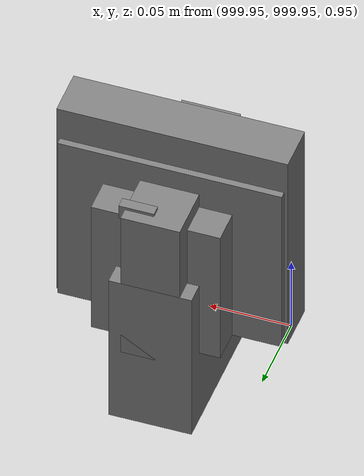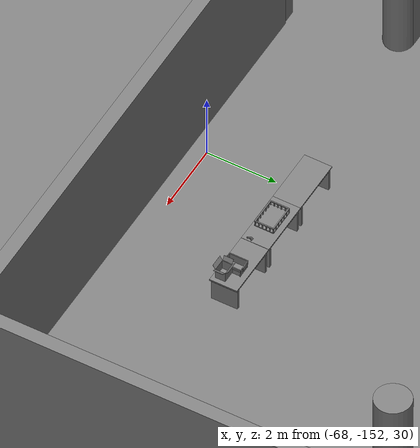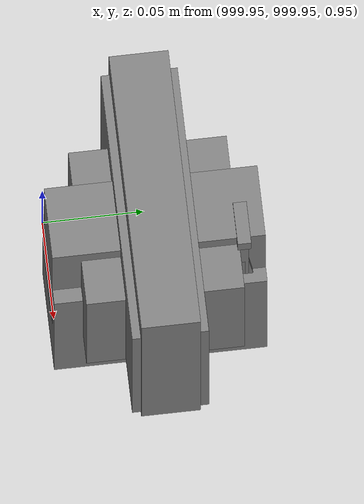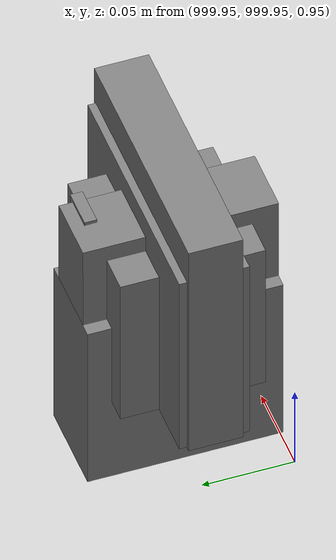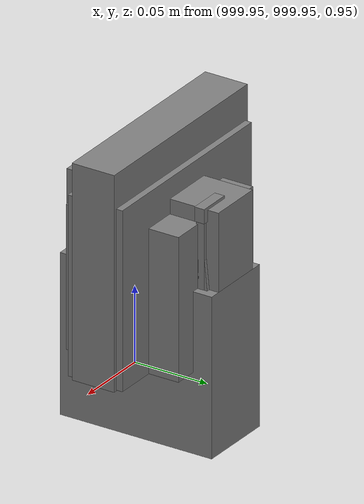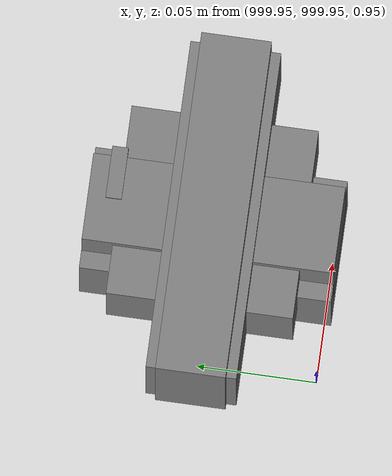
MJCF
<mujoco>
    <option gravity="0.000000000 0.000000000 -9.810000420" timestep="0.0049999999" integrator="implicitfast" density="1.225" viscosity="1.8000001e-05" noslip_iterations="10" iterations="100" sdf_iterations="50">
        <flag multiccd="disable"/>
    </option>
    <size memory="1000M"/>
    <compiler coordinate="local"/>
    <worldbody>
        <light cutoff="30" pos="0 1 1" dir="0 -1 -2"/>
        <light cutoff="30" pos="0 -1 1" dir="0 1 -2"/>
        <body pos="-64.866622925 -149.383972168 30.183746338" euler="89.999984741 89.999946594 0.000000000" name="openloong_gripper_2f85_fix_base_usda_bluebox_01">
            <geom contype="1" conaffinity="1" density="1000" type="box" material="" rgba="0.500000000 0.500000000 0.500000000 1.000000000" solimp="0.899999976 0.949999988 0.001000000" friction="1.000000000 0.005000000 0.000100000" solref="0.020000000 1.000000000" margin="0" condim="3" group="0" pos="0.276580811 0.187225342 0.000068665" quat="0.707106948 0.000077471 0.707106352 0.000077486" size="0.100000001 0.057999998 0.010000000" name="openloong_gripper_2f85_fix_base_usda_geom_84F57012_8F75_4102_AE2C_752FF968143B"/>
            <geom contype="1" conaffinity="1" density="1000" type="box" material="" rgba="0.500000000 0.500000000 0.500000000 1.000000000" solimp="0.899999976 0.949999988 0.001000000" friction="1.000000000 0.005000000 0.000100000" solref="0.020000000 1.000000000" margin="0" condim="3" group="0" pos="0.000000000 0.002883911 0.000000000" quat="0.999999881 0.000000000 0.000000000 0.000000000" size="0.254000008 0.003000000 0.172000006" name="openloong_gripper_2f85_fix_base_usda_geom_2211E574_E220_439E_A5E0_5B1DA8AE6FA6"/>
            <geom contype="1" conaffinity="1" density="1000" type="box" material="" rgba="0.500000000 0.500000000 0.500000000 1.000000000" solimp="0.899999976 0.949999988 0.001000000" friction="1.000000000 0.005000000 0.000100000" solref="0.020000000 1.000000000" margin="0" condim="3" group="0" pos="0.000000000 0.124874115 0.173484802" quat="0.999796331 0.020176515 -0.000000015 0.000000030" size="0.259999990 0.119999997 0.007000000" name="openloong_gripper_2f85_fix_base_usda_geom_EC8E034B_578C_41FB_9BFB_67F3764AFC50"/>
            <geom contype="1" conaffinity="1" density="1000" type="box" material="" rgba="0.500000000 0.500000000 0.500000000 1.000000000" solimp="0.899999976 0.949999988 0.001000000" friction="1.000000000 0.005000000 0.000100000" solref="0.020000000 1.000000000" margin="0" condim="3" group="0" pos="0.000000000 0.124874115 -0.173469543" quat="0.999796331 -0.020176545 -0.000000015 0.000000000" size="0.259999990 0.119999997 0.007000000" name="openloong_gripper_2f85_fix_base_usda_geom_E31875BD_1BD4_47CB_AAB3_A304EF2ECB5A"/>
            <geom contype="1" conaffinity="1" density="1000" type="box" material="" rgba="0.500000000 0.500000000 0.500000000 1.000000000" solimp="0.899999976 0.949999988 0.001000000" friction="1.000000000 0.005000000 0.000100000" solref="0.020000000 1.000000000" margin="0" condim="3" group="0" pos="0.000000000 0.214008331 0.188980103" quat="0.999912977 0.013176724 0.000000015 0.000000000" size="0.259999990 0.029999999 0.012500000" name="openloong_gripper_2f85_fix_base_usda_geom_A49F8949_3DD1_4548_9B10_044D40E65870"/>
            <geom contype="1" conaffinity="1" density="1000" type="box" material="" rgba="0.500000000 0.500000000 0.500000000 1.000000000" solimp="0.899999976 0.949999988 0.001000000" friction="1.000000000 0.005000000 0.000100000" solref="0.020000000 1.000000000" margin="0" condim="3" group="0" pos="-0.258361816 0.125289917 0.001876831" quat="0.702796936 -0.020792112 0.710783124 0.020769298" size="0.189999998 0.119999997 0.009000000" name="openloong_gripper_2f85_fix_base_usda_geom_AD8F9953_4945_44C8_A639_EEE614B6CA3F"/>
            <geom contype="1" conaffinity="1" density="1000" type="box" material="" rgba="0.500000000 0.500000000 0.500000000 1.000000000" solimp="0.899999976 0.949999988 0.001000000" friction="1.000000000 0.005000000 0.000100000" solref="0.020000000 1.000000000" margin="0" condim="3" group="0" pos="0.000000000 0.214008331 -0.188980103" quat="0.999912977 -0.013176769 0.000000030 0.000000015" size="0.259999990 0.029999999 0.012500000" name="openloong_gripper_2f85_fix_base_usda_geom_036F6AAB_4D1D_47F6_9E81_8C80BCCF58B0"/>
            <geom contype="1" conaffinity="1" density="1000" type="box" material="" rgba="0.500000000 0.500000000 0.500000000 1.000000000" solimp="0.899999976 0.949999988 0.001000000" friction="1.000000000 0.005000000 0.000100000" solref="0.020000000 1.000000000" margin="0" condim="3" group="0" pos="-0.276611328 0.187225342 0.000068665" quat="0.707106650 0.000077441 0.707106709 0.000077456" size="0.100000001 0.057999998 0.010000000" name="openloong_gripper_2f85_fix_base_usda_geom_E60098F7_8DE1_4AB8_BEAB_2BF78F79326F"/>
            <geom contype="1" conaffinity="1" density="1000" type="box" material="" rgba="0.500000000 0.500000000 0.500000000 1.000000000" solimp="0.899999976 0.949999988 0.001000000" friction="1.000000000 0.005000000 0.000100000" solref="0.020000000 1.000000000" margin="0" condim="3" group="0" pos="0.258331299 0.125289917 0.001876831" quat="0.702851415 0.018856421 0.710823774 -0.019329369" size="0.189999998 0.119999997 0.009000000" name="openloong_gripper_2f85_fix_base_usda_geom_470F813D_5089_4977_AB87_CCEB0651E51F"/>
            <freejoint name="openloong_gripper_2f85_fix_base_usda_bluebox_01_joint"/>
            <site size="0.005000000 0.005000000 0.005000000" rgba="0.500000000 0.500000000 0.500000000 1.000000000" pos="0.000000000 0.000000000 0.000000000" quat="0.999961913 0.008726534 0.000000000 0.000000000" group="0" type="sphere" name="openloong_gripper_2f85_fix_base_usda_bluebox_01site"/>
        </body>
        <body pos="-64.496299744 -149.491867065 30.235729218" euler="0.000000000 0.000000000 89.999946594" name="openloong_gripper_2f85_fix_base_usda_cardboardbox_01">
            <geom contype="1" conaffinity="1" density="1000" type="box" material="" rgba="0.500000000 0.500000000 0.500000000 1.000000000" solimp="0.899999976 0.949999988 0.001000000" friction="1.000000000 0.005000000 0.000100000" solref="0.020000000 1.000000000" margin="0" condim="3" group="0" pos="-0.003166199 -0.004086494 0.005052090" quat="1.000000000 0.000000000 0.000000000 0.000000000" size="0.142499998 0.177500010 0.005000000" name="openloong_gripper_2f85_fix_base_usda_geom_7E53FB41_6145_4B7E_BEF2_ED261CF01565"/>
            <geom contype="1" conaffinity="1" density="1000" type="box" material="" rgba="0.500000000 0.500000000 0.500000000 1.000000000" solimp="0.899999976 0.949999988 0.001000000" friction="1.000000000 0.005000000 0.000100000" solref="0.020000000 1.000000000" margin="0" condim="3" group="0" pos="-0.003166199 0.170316696 0.150570869" quat="1.000000000 0.000000000 0.000000000 0.000000000" size="0.142499998 0.005000000 0.149999991" name="openloong_gripper_2f85_fix_base_usda_geom_49261835_7DCD_403D_BDB6_DF18DEB51BD4"/>
            <geom contype="1" conaffinity="1" density="1000" type="box" material="" rgba="0.500000000 0.500000000 0.500000000 1.000000000" solimp="0.899999976 0.949999988 0.001000000" friction="1.000000000 0.005000000 0.000100000" solref="0.020000000 1.000000000" margin="0" condim="3" group="0" pos="-0.147399902 -0.005307198 0.150570869" quat="1.000000000 0.000000000 0.000000000 0.000000000" size="0.005000000 0.177500010 0.149999991" name="openloong_gripper_2f85_fix_base_usda_geom_061EF2E1_8B5A_4973_B4CE_F5E1B29695F3"/>
            <geom contype="1" conaffinity="1" density="1000" type="box" material="" rgba="0.500000000 0.500000000 0.500000000 1.000000000" solimp="0.899999976 0.949999988 0.001000000" friction="1.000000000 0.005000000 0.000100000" solref="0.020000000 1.000000000" margin="0" condim="3" group="0" pos="0.140275955 -0.005307198 0.150570869" quat="1.000000000 0.000000000 0.000000000 0.000000000" size="0.005000000 0.177500010 0.149999991" name="openloong_gripper_2f85_fix_base_usda_geom_50DA35F8_01D0_4233_9BF6_9092B52370A9"/>
            <geom contype="1" conaffinity="1" density="1000" type="box" material="" rgba="0.500000000 0.500000000 0.500000000 1.000000000" solimp="0.899999976 0.949999988 0.001000000" friction="1.000000000 0.005000000 0.000100000" solref="0.020000000 1.000000000" margin="0" condim="3" group="0" pos="-0.003166199 -0.181550980 0.150570869" quat="1.000000000 0.000000000 0.000000000 0.000000000" size="0.142499998 0.005000000 0.149999991" name="openloong_gripper_2f85_fix_base_usda_geom_2B6DC4AD_8222_4182_9146_75FB867872AB"/>
            <freejoint name="openloong_gripper_2f85_fix_base_usda_cardboardbox_01_joint"/>
            <site size="0.005000000 0.005000000 0.005000000" rgba="0.500000000 0.500000000 0.500000000 1.000000000" pos="0.000000000 0.000000000 0.000000000" quat="0.999961913 0.008726535 0.000000000 0.000000000" group="0" type="sphere" name="openloong_gripper_2f85_fix_base_usda_site_9D7F59B6_FC87_4727_85C4_C1363CAFE563"/>
            <body pos="0.139160156 -0.004048347 0.301930904" euler="-179.999954224 49.383502960 179.999954224" name="openloong_gripper_2f85_fix_base_usda_A1_006">
                <geom contype="1" conaffinity="1" density="1000" type="box" material="" rgba="0.500000000 0.500000000 0.500000000 1.000000000" solimp="0.899999976 0.949999988 0.001000000" friction="1.000000000 0.005000000 0.000100000" solref="0.020000000 1.000000000" margin="0" condim="3" group="0" pos="-0.071587563 0.000009537 0.001745224" quat="0.999999881 0.000000000 0.000000000 0.000000000" size="0.071249999 0.179999992 0.002500000" name="openloong_gripper_2f85_fix_base_usda_geom_26506A05_D04C_4878_B913_FCB8C270423C"/>
                <joint armature="0" stiffness="0.07" damping="0.0099999998" axis="0.000000 1.000000 0.000000" type="hinge" name="openloong_gripper_2f85_fix_base_usda_A1_006"/>
            </body>
            <body pos="-0.145902634 -0.004086494 0.301938057" euler="-180.000000000 -60.000011444 -180.000000000" name="openloong_gripper_2f85_fix_base_usda_A2_006">
                <geom contype="1" conaffinity="1" density="1000" type="box" material="" rgba="0.500000000 0.500000000 0.500000000 1.000000000" solimp="0.899999976 0.949999988 0.001000000" friction="1.000000000 0.005000000 0.000100000" solref="0.020000000 1.000000000" margin="0" condim="3" group="0" pos="0.071268082 0.000009537 0.002717972" quat="0.000002921 0.000000000 -0.000000030 0.999999881" size="0.071249999 0.179999992 0.002500000" name="openloong_gripper_2f85_fix_base_usda_geom_4DD78DF9_CE49_4B88_AF29_DD5129D38D19"/>
                <joint armature="0" stiffness="0.07" damping="0.0099999998" axis="0.000000 1.000000 0.000000" type="hinge" name="openloong_gripper_2f85_fix_base_usda_A2_006"/>
            </body>
            <body pos="-0.003385544 0.175991058 0.301930904" euler="-125.858116150 -0.000004561 0.000002331" name="openloong_gripper_2f85_fix_base_usda_B2_006">
                <geom contype="1" conaffinity="1" density="1000" type="box" material="" rgba="0.500000000 0.500000000 0.500000000 1.000000000" solimp="0.899999976 0.949999988 0.001000000" friction="1.000000000 0.005000000 0.000100000" solref="0.020000000 1.000000000" margin="0" condim="3" group="0" pos="0.000009537 -0.070939064 -0.002470016" quat="0.999614120 0.027776197 -0.000000015 0.000000030" size="0.137500003 0.064999998 0.005000000" name="openloong_gripper_2f85_fix_base_usda_geom_5DF9F90A_3416_4A53_B7ED_B4C06FA7A415"/>
                <joint armature="0" stiffness="0.07" damping="0.0099999998" axis="1.000000 0.000000 0.000000" type="hinge" name="openloong_gripper_2f85_fix_base_usda_B2_006"/>
            </body>
            <body pos="-0.003385544 -0.184140205 0.301938057" euler="147.805557251 0.000000000 0.000000000" name="openloong_gripper_2f85_fix_base_usda_B1_006">
                <geom contype="1" conaffinity="1" density="1000" type="box" material="" rgba="0.500000000 0.500000000 0.500000000 1.000000000" solimp="0.899999976 0.949999988 0.001000000" friction="1.000000000 0.005000000 0.000100000" solref="0.020000000 1.000000000" margin="0" condim="3" group="0" pos="-0.000028610 0.070202351 -0.002703667" quat="0.999614179 -0.027776167 0.000000000 0.000000000" size="0.137500003 0.064999998 0.005000000" name="openloong_gripper_2f85_fix_base_usda_geom_5FFAA4CB_C756_4010_89BA_E18050AE198B"/>
                <joint armature="0" stiffness="0.07" damping="0.0099999998" axis="1.000000 0.000000 0.000000" type="hinge" name="openloong_gripper_2f85_fix_base_usda_B1_006"/>
            </body>
        </body>
        <body pos="-65.882858276 -149.481979370 30.229999542" euler="-64.487716675 0.000000000 0.000000000" name="openloong_gripper_2f85_fix_base_usda_Barcode">
            <geom contype="1" conaffinity="1" density="1000" type="box" material="" rgba="0.500000000 0.500000000 0.500000000 1.000000000" solimp="0.899999976 0.949999988 0.001000000" friction="1.000000000 0.005000000 0.000100000" solref="0.020000000 1.000000000" margin="0" condim="3" group="0" pos="0.000000000 0.013038635 0.001419067" quat="0.000000000 0.000000000 0.000000000 1.000000119" size="0.034000002 0.010000000 0.017999999" name="openloong_gripper_2f85_fix_base_usda_geom_4CF884BB_46CE_44BF_81FF_68AD864566DB"/>
            <geom contype="1" conaffinity="1" density="1000" type="box" material="" rgba="0.500000000 0.500000000 0.500000000 1.000000000" solimp="0.899999976 0.949999988 0.001000000" friction="1.000000000 0.005000000 0.000100000" solref="0.020000000 1.000000000" margin="0" condim="3" group="0" pos="0.000000000 -0.035301208 -0.007095337" quat="0.000000000 0.000000000 -0.043619365 0.999048233" size="0.028999999 0.010000000 0.020000000" name="openloong_gripper_2f85_fix_base_usda_geom_74EE9964_5B19_4171_A9E3_28931D84880E"/>
            <geom contype="1" conaffinity="1" density="1000" type="box" material="" rgba="0.500000000 0.500000000 0.500000000 1.000000000" solimp="0.899999976 0.949999988 0.001000000" friction="1.000000000 0.005000000 0.000100000" solref="0.020000000 1.000000000" margin="0" condim="3" group="0" pos="0.000000000 -0.043411255 -0.011749268" quat="0.922262907 0.386563420 0.000000000 0.000000000" size="0.026000001 0.010000000 0.020000000" name="openloong_gripper_2f85_fix_base_usda_geom_1AE4324D_D0FB_45B1_89B1_773F981C387B"/>
            <geom contype="1" conaffinity="1" density="1000" type="box" material="" rgba="0.500000000 0.500000000 0.500000000 1.000000000" solimp="0.899999976 0.949999988 0.001000000" friction="1.000000000 0.005000000 0.000100000" solref="0.020000000 1.000000000" margin="0" condim="3" group="0" pos="0.000000000 -0.016967773 -0.031860352" quat="0.000000000 0.000000000 0.000000000 1.000000119" size="0.008000000 0.010000000 0.013000000" name="openloong_gripper_2f85_fix_base_usda_geom_76479193_68DA_4593_B7BE_0FAE24F5AD24"/>
            <geom contype="1" conaffinity="1" density="1000" type="box" material="" rgba="0.500000000 0.500000000 0.500000000 1.000000000" solimp="0.899999976 0.949999988 0.001000000" friction="1.000000000 0.005000000 0.000100000" solref="0.020000000 1.000000000" margin="0" condim="3" group="0" pos="0.000000000 -0.001869202 0.000312805" quat="0.953716993 0.300705761 0.000000000 0.000000000" size="0.032000002 0.010000000 0.018999999" name="openloong_gripper_2f85_fix_base_usda_geom_82145521_EB4E_48FF_903D_26935C451121"/>
            <geom contype="1" conaffinity="1" density="1000" type="box" material="" rgba="0.500000000 0.500000000 0.500000000 1.000000000" solimp="0.899999976 0.949999988 0.001000000" friction="1.000000000 0.005000000 0.000100000" solref="0.020000000 1.000000000" margin="0" condim="3" group="0" pos="0.000000000 -0.019531250 -0.003173828" quat="0.953716993 0.300705761 0.000000000 0.000000000" size="0.030999999 0.010000000 0.020000000" name="openloong_gripper_2f85_fix_base_usda_geom_5459B659_FEA9_4DD3_A3B0_D5C7058724BD"/>
            <geom contype="1" conaffinity="1" density="1000" type="box" material="" rgba="0.500000000 0.500000000 0.500000000 1.000000000" solimp="0.899999976 0.949999988 0.001000000" friction="1.000000000 0.005000000 0.000100000" solref="0.020000000 1.000000000" margin="0" condim="3" group="0" pos="0.000000000 -0.035301208 -0.007095337" quat="0.953716993 0.300705761 0.000000000 0.000000000" size="0.028999999 0.010000000 0.020000000" name="openloong_gripper_2f85_fix_base_usda_geom_F682628D_E2F9_40A0_98EB_8FFA0DD65505"/>
            <geom contype="1" conaffinity="1" density="1000" type="box" material="" rgba="0.500000000 0.500000000 0.500000000 1.000000000" solimp="0.899999976 0.949999988 0.001000000" friction="1.000000000 0.005000000 0.000100000" solref="0.020000000 1.000000000" margin="0" condim="3" group="0" pos="0.000000000 -0.042617798 -0.071121216" quat="0.000000000 0.000000000 0.000000000 1.000000119" size="0.013000000 0.021000000 0.059999999" name="openloong_gripper_2f85_fix_base_usda_geom_793BA28D_F7CB_4459_8C1B_87C428C2F7AD"/>
            <freejoint name="openloong_gripper_2f85_fix_base_usda_Barcode_joint"/>
            <site size="0.005000000 0.005000000 0.005000000" rgba="0.500000000 0.500000000 0.500000000 1.000000000" pos="0.000000000 0.000000000 0.000000000" quat="1.000000000 0.000000000 0.000000000 0.000000000" group="0" type="sphere" name="openloong_gripper_2f85_fix_base_usda_Barcode_site"/>
        </body>
        <body pos="-66.745018005 -149.392349243 30.184000015" euler="0.000000000 0.000000000 89.999946594" name="[22329926149577]_Basket_01">
            <geom contype="1" conaffinity="1" density="1000" type="box" material="" rgba="0.500000000 0.500000000 0.500000000 1.000000000" solimp="0.899999976 0.949999988 0.001000000" friction="1.000000000 0.005000000 0.000100000" solref="0.020000000 1.000000000" margin="0" condim="3" group="0" pos="-0.052425385 0.389207840 0.089787483" quat="0.707107008 0.000000000 0.000000000 0.707106411" size="0.014249999 0.014249999 0.059999999" name="[22329926149577]_geom_34226BE1_6A1E_4670_86D0_D77E680D7327"/>
            <geom contype="1" conaffinity="1" density="1000" type="box" material="" rgba="0.500000000 0.500000000 0.500000000 1.000000000" solimp="0.899999976 0.949999988 0.001000000" friction="1.000000000 0.005000000 0.000100000" solref="0.020000000 1.000000000" margin="0" condim="3" group="0" pos="0.264015198 -0.133043289 0.089787483" quat="0.707107008 0.000000000 0.000000000 0.707106411" size="0.014249999 0.014249999 0.059999999" name="[22329926149577]_geom_F1E6CB2E_5C98_4F7C_83C8_0E7AB57B369B"/>
            <geom contype="1" conaffinity="1" density="1000" type="box" material="" rgba="0.500000000 0.500000000 0.500000000 1.000000000" solimp="0.899999976 0.949999988 0.001000000" friction="1.000000000 0.005000000 0.000100000" solref="0.020000000 1.000000000" margin="0" condim="3" group="0" pos="-0.264015198 -0.265548706 0.089793205" quat="0.707107008 0.000000000 0.000000000 0.707106411" size="0.014249999 0.014249999 0.059999999" name="[22329926149577]_geom_9295DB49_6C3D_48D9_BFA9_8A26A892D73C"/>
            <geom contype="1" conaffinity="1" density="1000" type="box" material="" rgba="0.500000000 0.500000000 0.500000000 1.000000000" solimp="0.899999976 0.949999988 0.001000000" friction="1.000000000 0.005000000 0.000100000" solref="0.020000000 1.000000000" margin="0" condim="3" group="0" pos="-0.160263062 -0.389322281 0.089793205" quat="0.707107008 0.000000000 0.000000000 0.707106411" size="0.014249999 0.014249999 0.059999999" name="[22329926149577]_geom_DF7D998C_D467_42A8_AFFC_06014081A45B"/>
            <geom contype="1" conaffinity="1" density="1000" type="box" material="" rgba="0.500000000 0.500000000 0.500000000 1.000000000" solimp="0.899999976 0.949999988 0.001000000" friction="1.000000000 0.005000000 0.000100000" solref="0.020000000 1.000000000" margin="0" condim="3" group="0" pos="0.162265778 -0.389322281 0.089787483" quat="0.707107008 0.000000000 0.000000000 0.707106411" size="0.014249999 0.014249999 0.059999999" name="[22329926149577]_geom_AA2828CC_73F7_428C_B7DA_8DB5629D26C6"/>
            <geom contype="1" conaffinity="1" density="1000" type="box" material="" rgba="0.500000000 0.500000000 0.500000000 1.000000000" solimp="0.899999976 0.949999988 0.001000000" friction="1.000000000 0.005000000 0.000100000" solref="0.020000000 1.000000000" margin="0" condim="3" group="0" pos="0.264015198 0.389207840 0.089787483" quat="0.707107008 0.000000000 0.000000000 0.707106411" size="0.014249999 0.014249999 0.059999999" name="[22329926149577]_geom_AD161DCA_E028_43B3_9C84_65722C8E0EFA"/>
            <geom contype="1" conaffinity="1" density="1000" type="box" material="" rgba="0.500000000 0.500000000 0.500000000 1.000000000" solimp="0.899999976 0.949999988 0.001000000" friction="1.000000000 0.005000000 0.000100000" solref="0.020000000 1.000000000" margin="0" condim="3" group="0" pos="-0.264015198 -0.133043289 0.089793205" quat="0.707107008 0.000000000 0.000000000 0.707106411" size="0.014249999 0.014249999 0.059999999" name="[22329926149577]_geom_A08E616A_DCD8_448B_A373_C0F6BC8E6AD6"/>
            <geom contype="1" conaffinity="1" density="1000" type="box" material="" rgba="0.500000000 0.500000000 0.500000000 1.000000000" solimp="0.899999976 0.949999988 0.001000000" friction="1.000000000 0.005000000 0.000100000" solref="0.020000000 1.000000000" margin="0" condim="3" group="0" pos="-0.264026642 0.269256592 0.089793205" quat="0.707107008 0.000000000 0.000000000 0.707106411" size="0.014249999 0.014249999 0.059999999" name="[22329926149577]_geom_5C27BA04_6507_4F87_A658_B31BF44601AF"/>
            <geom contype="1" conaffinity="1" density="1000" type="box" material="" rgba="0.500000000 0.500000000 0.500000000 1.000000000" solimp="0.899999976 0.949999988 0.001000000" friction="1.000000000 0.005000000 0.000100000" solref="0.020000000 1.000000000" margin="0" condim="3" group="0" pos="0.054462433 0.389207840 0.089787483" quat="0.707107008 0.000000000 0.000000000 0.707106411" size="0.014249999 0.014249999 0.059999999" name="[22329926149577]_geom_C450E404_85BF_4A5F_B3E5_A7959298E024"/>
            <geom contype="1" conaffinity="1" density="1000" type="box" material="" rgba="0.500000000 0.500000000 0.500000000 1.000000000" solimp="0.899999976 0.949999988 0.001000000" friction="1.000000000 0.005000000 0.000100000" solref="0.020000000 1.000000000" margin="0" condim="3" group="0" pos="0.054462433 -0.389322281 0.089787483" quat="0.707107008 0.000000000 0.000000000 0.707106411" size="0.014249999 0.014249999 0.059999999" name="[22329926149577]_geom_A2140572_DB7E_4725_86C6_031F7CFDEC2A"/>
            <geom contype="1" conaffinity="1" density="1000" type="box" material="" rgba="0.500000000 0.500000000 0.500000000 1.000000000" solimp="0.899999976 0.949999988 0.001000000" friction="1.000000000 0.005000000 0.000100000" solref="0.020000000 1.000000000" margin="0" condim="3" group="0" pos="0.264015198 0.269256592 0.089793205" quat="0.707107008 0.000000000 0.000000000 0.707106411" size="0.014249999 0.014249999 0.059999999" name="[22329926149577]_geom_482D3058_617E_4F1C_B8ED_DA0AC0BC4525"/>
            <geom contype="1" conaffinity="1" density="1000" type="box" material="" rgba="0.500000000 0.500000000 0.500000000 1.000000000" solimp="0.899999976 0.949999988 0.001000000" friction="1.000000000 0.005000000 0.000100000" solref="0.020000000 1.000000000" margin="0" condim="3" group="0" pos="0.264015198 -0.389322281 0.089787483" quat="0.707107008 0.000000000 0.000000000 0.707106411" size="0.014249999 0.014249999 0.059999999" name="[22329926149577]_geom_B4F71493_B7FC_4696_A3A4_CDE2389AC8FE"/>
            <geom contype="1" conaffinity="1" density="1000" type="box" material="" rgba="0.500000000 0.500000000 0.500000000 1.000000000" solimp="0.899999976 0.949999988 0.001000000" friction="1.000000000 0.005000000 0.000100000" solref="0.020000000 1.000000000" margin="0" condim="3" group="0" pos="0.000000000 0.000000000 0.015998840" quat="0.707107008 0.000000000 0.000000000 0.707106411" size="0.403499991 0.279000014 0.015750000" name="[22329926149577]_geom_5E62C6EC_5FD9_4E51_8FBF_B73626AC0F97"/>
            <geom contype="1" conaffinity="1" density="1000" type="box" material="" rgba="0.500000000 0.500000000 0.500000000 1.000000000" solimp="0.899999976 0.949999988 0.001000000" friction="1.000000000 0.005000000 0.000100000" solref="0.020000000 1.000000000" margin="0" condim="3" group="0" pos="0.000000000 -0.389476776 0.163619041" quat="0.707107008 0.000000000 0.000000000 0.707106411" size="0.015000000 0.277500004 0.015750000" name="[22329926149577]_geom_B940995A_BC90_4648_88D9_5F7D1FBEC03C"/>
            <geom contype="1" conaffinity="1" density="1000" type="box" material="" rgba="0.500000000 0.500000000 0.500000000 1.000000000" solimp="0.899999976 0.949999988 0.001000000" friction="1.000000000 0.005000000 0.000100000" solref="0.020000000 1.000000000" margin="0" condim="3" group="0" pos="0.162265778 0.389207840 0.089787483" quat="0.707107008 0.000000000 0.000000000 0.707106411" size="0.014249999 0.014249999 0.059999999" name="[22329926149577]_geom_7A1773C0_A886_408D_8B59_0CA42C41D35F"/>
            <geom contype="1" conaffinity="1" density="1000" type="box" material="" rgba="0.500000000 0.500000000 0.500000000 1.000000000" solimp="0.899999976 0.949999988 0.001000000" friction="1.000000000 0.005000000 0.000100000" solref="0.020000000 1.000000000" margin="0" condim="3" group="0" pos="0.000000000 0.389471054 0.163619041" quat="0.707107008 0.000000000 0.000000000 0.707106411" size="0.015000000 0.277500004 0.015750000" name="[22329926149577]_geom_BC4BEDAA_B181_4B4D_97FB_03C572F4F962"/>
            <geom contype="1" conaffinity="1" density="1000" type="box" material="" rgba="0.500000000 0.500000000 0.500000000 1.000000000" solimp="0.899999976 0.949999988 0.001000000" friction="1.000000000 0.005000000 0.000100000" solref="0.020000000 1.000000000" margin="0" condim="3" group="0" pos="-0.263511658 0.000000000 0.163619041" quat="0.707107008 0.000000000 0.000000000 0.707106411" size="0.403499991 0.015000000 0.015750000" name="[22329926149577]_geom_22FF602A_8C27_4073_9E43_10186D98B3B6"/>
            <geom contype="1" conaffinity="1" density="1000" type="box" material="" rgba="0.500000000 0.500000000 0.500000000 1.000000000" solimp="0.899999976 0.949999988 0.001000000" friction="1.000000000 0.005000000 0.000100000" solref="0.020000000 1.000000000" margin="0" condim="3" group="0" pos="-0.264015198 0.141334534 0.089793205" quat="0.707107008 0.000000000 0.000000000 0.707106411" size="0.014249999 0.014249999 0.059999999" name="[22329926149577]_geom_F9E1A918_160C_4A23_85EA_E839D479BE1E"/>
            <geom contype="1" conaffinity="1" density="1000" type="box" material="" rgba="0.500000000 0.500000000 0.500000000 1.000000000" solimp="0.899999976 0.949999988 0.001000000" friction="1.000000000 0.005000000 0.000100000" solref="0.020000000 1.000000000" margin="0" condim="3" group="0" pos="0.264015198 -0.265548706 0.089787483" quat="0.707107008 0.000000000 0.000000000 0.707106411" size="0.014249999 0.014249999 0.059999999" name="[22329926149577]_geom_C8BAB4D3_CE24_442A_8942_4D5AA4BF374D"/>
            <geom contype="1" conaffinity="1" density="1000" type="box" material="" rgba="0.500000000 0.500000000 0.500000000 1.000000000" solimp="0.899999976 0.949999988 0.001000000" friction="1.000000000 0.005000000 0.000100000" solref="0.020000000 1.000000000" margin="0" condim="3" group="0" pos="-0.160263062 0.389207840 0.089787483" quat="0.707107008 0.000000000 0.000000000 0.707106411" size="0.014249999 0.014249999 0.059999999" name="[22329926149577]_geom_43D6E8F3_2D5D_4FD9_BBA8_A1A635A65868"/>
            <geom contype="1" conaffinity="1" density="1000" type="box" material="" rgba="0.500000000 0.500000000 0.500000000 1.000000000" solimp="0.899999976 0.949999988 0.001000000" friction="1.000000000 0.005000000 0.000100000" solref="0.020000000 1.000000000" margin="0" condim="3" group="0" pos="-0.052425385 -0.389322281 0.089787483" quat="0.707107008 0.000000000 0.000000000 0.707106411" size="0.014249999 0.014249999 0.059999999" name="[22329926149577]_geom_A727F8F8_88FD_42BA_9E9D_4B86F97615D9"/>
            <geom contype="1" conaffinity="1" density="1000" type="box" material="" rgba="0.500000000 0.500000000 0.500000000 1.000000000" solimp="0.899999976 0.949999988 0.001000000" friction="1.000000000 0.005000000 0.000100000" solref="0.020000000 1.000000000" margin="0" condim="3" group="0" pos="-0.264026642 -0.389322281 0.089793205" quat="0.707107008 0.000000000 0.000000000 0.707106411" size="0.014249999 0.014249999 0.059999999" name="[22329926149577]_geom_1F5EB5D0_9B3C_4A6F_9775_5363959AC956"/>
            <geom contype="1" conaffinity="1" density="1000" type="box" material="" rgba="0.500000000 0.500000000 0.500000000 1.000000000" solimp="0.899999976 0.949999988 0.001000000" friction="1.000000000 0.005000000 0.000100000" solref="0.020000000 1.000000000" margin="0" condim="3" group="0" pos="0.264015198 0.141334534 0.089787483" quat="0.707107008 0.000000000 0.000000000 0.707106411" size="0.014249999 0.014249999 0.059999999" name="[22329926149577]_geom_9A992DC5_DF45_46BA_8881_90388CCACCD1"/>
            <geom contype="1" conaffinity="1" density="1000" type="box" material="" rgba="0.500000000 0.500000000 0.500000000 1.000000000" solimp="0.899999976 0.949999988 0.001000000" friction="1.000000000 0.005000000 0.000100000" solref="0.020000000 1.000000000" margin="0" condim="3" group="0" pos="-0.264015198 0.389207840 0.089793205" quat="0.707107008 0.000000000 0.000000000 0.707106411" size="0.014249999 0.014249999 0.059999999" name="[22329926149577]_geom_16632498_A770_49BD_9F28_E1CD37FB1D91"/>
            <geom contype="1" conaffinity="1" density="1000" type="box" material="" rgba="0.500000000 0.500000000 0.500000000 1.000000000" solimp="0.899999976 0.949999988 0.001000000" friction="1.000000000 0.005000000 0.000100000" solref="0.020000000 1.000000000" margin="0" condim="3" group="0" pos="0.264015198 0.004480362 0.089787483" quat="0.707107008 0.000000000 0.000000000 0.707106411" size="0.014249999 0.014249999 0.059999999" name="[22329926149577]_geom_EF0B9132_8C43_401C_9CFF_E0E56B05E1EE"/>
            <geom contype="1" conaffinity="1" density="1000" type="box" material="" rgba="0.500000000 0.500000000 0.500000000 1.000000000" solimp="0.899999976 0.949999988 0.001000000" friction="1.000000000 0.005000000 0.000100000" solref="0.020000000 1.000000000" margin="0" condim="3" group="0" pos="0.263694763 -0.000011444 0.163619041" quat="0.707107008 0.000000000 0.000000000 0.707106411" size="0.403499991 0.015000000 0.015750000" name="[22329926149577]_geom_F9C22011_0B4D_400F_AE62_5531A0B4E63C"/>
            <geom contype="1" conaffinity="1" density="1000" type="box" material="" rgba="0.500000000 0.500000000 0.500000000 1.000000000" solimp="0.899999976 0.949999988 0.001000000" friction="1.000000000 0.005000000 0.000100000" solref="0.020000000 1.000000000" margin="0" condim="3" group="0" pos="-0.264015198 0.004480362 0.089793205" quat="0.707107008 0.000000000 0.000000000 0.707106411" size="0.014249999 0.014249999 0.059999999" name="[22329926149577]_geom_F282E4F7_982F_4BEF_8B48_2E268A45C753"/>
            <freejoint name="[22329926149577]_joint_1DF05D3D_6BE2_4EC6_9CB8_5F632D8869E8"/>
        </body>
        <body pos="0.000000000 0.000000000 0.000000000" euler="0.000000000 0.000000000 0.000000000" name="Static Objects_Static Objects">
            <geom contype="1" conaffinity="1" density="1000" type="box" material="" rgba="0.500000000 0.500000000 0.500000000 1.000000000" solimp="0.899999976 0.949999988 0.001000000" friction="1.000000000 0.005000000 0.000100000" solref="0.020000000 1.000000000" margin="0" condim="3" group="0" pos="-67.544113159 -149.365814209 29.727830887" quat="0.500000417 0.499999970 0.499999553 0.499999970" size="0.381000012 0.319999993 0.041000001" name="Static Objects_geom_83CD2F7B_E64D_4DAB_B821_B98A0FFAA2AB"/>
            <geom contype="1" conaffinity="1" density="1000" type="box" material="" rgba="0.500000000 0.500000000 0.500000000 1.000000000" solimp="0.899999976 0.949999988 0.001000000" friction="1.000000000 0.005000000 0.000100000" solref="0.020000000 1.000000000" margin="0" condim="3" group="0" pos="-68.239501953 -149.365814209 30.086868286" quat="0.500000417 0.499999970 0.499999553 0.499999970" size="0.370999992 0.039500002 0.745000005" name="Static Objects_geom_4416C74C_F676_4521_8F2C_01B29E08D3AB"/>
            <geom contype="1" conaffinity="1" density="1000" type="box" material="" rgba="0.500000000 0.500000000 0.500000000 1.000000000" solimp="0.899999976 0.949999988 0.001000000" friction="1.000000000 0.005000000 0.000100000" solref="0.020000000 1.000000000" margin="0" condim="3" group="0" pos="-68.239501953 -149.365814209 30.147235870" quat="0.500000417 0.499999970 0.499999553 0.499999970" size="0.400000006 0.022000000 0.800000012" name="Static Objects_geom_965B5939_B615_411A_BD3A_C21E74209BCC"/>
            <geom contype="1" conaffinity="1" density="1000" type="box" material="" rgba="0.500000000 0.500000000 0.500000000 1.000000000" solimp="0.899999976 0.949999988 0.001000000" friction="1.000000000 0.005000000 0.000100000" solref="0.020000000 1.000000000" margin="0" condim="3" group="0" pos="-68.934890747 -149.365814209 29.727830887" quat="0.500000417 0.499999970 0.499999553 0.499999970" size="0.381000012 0.319999993 0.041000001" name="Static Objects_geom_3D6B1835_BE4F_430A_AE59_8CB107489951"/>
            <geom contype="1" conaffinity="1" density="1000" type="box" material="" rgba="0.500000000 0.500000000 0.500000000 1.000000000" solimp="0.899999976 0.949999988 0.001000000" friction="1.000000000 0.005000000 0.000100000" solref="0.020000000 1.000000000" margin="0" condim="3" group="0" pos="-68.239501953 -149.365814209 29.561563492" quat="0.500000417 0.499999970 0.499999553 0.499999970" size="0.020000000 0.022000000 0.660000026" name="Static Objects_geom_A2B5D3E9_4661_4F9A_B8B9_68AEBBEBAF29"/>
            <geom contype="1" conaffinity="1" density="1000" type="box" material="" rgba="0.500000000 0.500000000 0.500000000 1.000000000" solimp="0.899999976 0.949999988 0.001000000" friction="1.000000000 0.005000000 0.000100000" solref="0.020000000 1.000000000" margin="0" condim="3" group="0" pos="-65.945671082 -149.365814209 29.727830887" quat="0.500000417 0.499999970 0.499999553 0.499999970" size="0.381000012 0.319999993 0.041000001" name="Static Objects_geom_4C3A812E_C0F0_4F04_9FAF_2F801A9D81A4"/>
            <geom contype="1" conaffinity="1" density="1000" type="box" material="" rgba="0.500000000 0.500000000 0.500000000 1.000000000" solimp="0.899999976 0.949999988 0.001000000" friction="1.000000000 0.005000000 0.000100000" solref="0.020000000 1.000000000" margin="0" condim="3" group="0" pos="-66.641059875 -149.365814209 30.086868286" quat="0.500000417 0.499999970 0.499999553 0.499999970" size="0.370999992 0.039500002 0.745000005" name="Static Objects_geom_0029D9E5_785E_4472_9586_EEF22DD77614"/>
            <geom contype="1" conaffinity="1" density="1000" type="box" material="" rgba="0.500000000 0.500000000 0.500000000 1.000000000" solimp="0.899999976 0.949999988 0.001000000" friction="1.000000000 0.005000000 0.000100000" solref="0.020000000 1.000000000" margin="0" condim="3" group="0" pos="-66.641059875 -149.365814209 30.147235870" quat="0.500000417 0.499999970 0.499999553 0.499999970" size="0.400000006 0.022000000 0.800000012" name="Static Objects_geom_EE520902_2B6C_4E8A_9CDC_3FD67379A47C"/>
            <geom contype="1" conaffinity="1" density="1000" type="box" material="" rgba="0.500000000 0.500000000 0.500000000 1.000000000" solimp="0.899999976 0.949999988 0.001000000" friction="1.000000000 0.005000000 0.000100000" solref="0.020000000 1.000000000" margin="0" condim="3" group="0" pos="-67.336448669 -149.365814209 29.727830887" quat="0.500000417 0.499999970 0.499999553 0.499999970" size="0.381000012 0.319999993 0.041000001" name="Static Objects_geom_A946558A_12D8_430B_9AB0_16D11F3D4780"/>
            <geom contype="1" conaffinity="1" density="1000" type="box" material="" rgba="0.500000000 0.500000000 0.500000000 1.000000000" solimp="0.899999976 0.949999988 0.001000000" friction="1.000000000 0.005000000 0.000100000" solref="0.020000000 1.000000000" margin="0" condim="3" group="0" pos="-66.641059875 -149.365814209 29.561563492" quat="0.500000417 0.499999970 0.499999553 0.499999970" size="0.020000000 0.022000000 0.660000026" name="Static Objects_geom_47EE418C_1794_455E_9EAC_A311B54FA7C1"/>
            <geom contype="1" conaffinity="1" density="1000" type="box" material="" rgba="0.500000000 0.500000000 0.500000000 1.000000000" solimp="0.899999976 0.949999988 0.001000000" friction="1.000000000 0.005000000 0.000100000" solref="0.020000000 1.000000000" margin="0" condim="3" group="0" pos="-64.338577271 -149.365814209 29.727830887" quat="0.500000417 0.499999970 0.499999553 0.499999970" size="0.381000012 0.319999993 0.041000001" name="Static Objects_geom_3FEA1C7F_20C7_4AC3_84BB_033B3D42D7BA"/>
            <geom contype="1" conaffinity="1" density="1000" type="box" material="" rgba="0.500000000 0.500000000 0.500000000 1.000000000" solimp="0.899999976 0.949999988 0.001000000" friction="1.000000000 0.005000000 0.000100000" solref="0.020000000 1.000000000" margin="0" condim="3" group="0" pos="-65.033966064 -149.365814209 30.086868286" quat="0.500000417 0.499999970 0.499999553 0.499999970" size="0.370999992 0.039500002 0.745000005" name="Static Objects_geom_CECC0904_A7EF_40DD_B74C_E6E2F1EEA643"/>
            <geom contype="1" conaffinity="1" density="1000" type="box" material="" rgba="0.500000000 0.500000000 0.500000000 1.000000000" solimp="0.899999976 0.949999988 0.001000000" friction="1.000000000 0.005000000 0.000100000" solref="0.020000000 1.000000000" margin="0" condim="3" group="0" pos="-65.033966064 -149.365814209 30.147235870" quat="0.500000417 0.499999970 0.499999553 0.499999970" size="0.400000006 0.022000000 0.800000012" name="Static Objects_geom_E9DEF9AE_A586_47B9_B411_097DC039F04D"/>
            <geom contype="1" conaffinity="1" density="1000" type="box" material="" rgba="0.500000000 0.500000000 0.500000000 1.000000000" solimp="0.899999976 0.949999988 0.001000000" friction="1.000000000 0.005000000 0.000100000" solref="0.020000000 1.000000000" margin="0" condim="3" group="0" pos="-65.729354858 -149.365814209 29.727830887" quat="0.500000417 0.499999970 0.499999553 0.499999970" size="0.381000012 0.319999993 0.041000001" name="Static Objects_geom_0206C534_287D_42CD_95A5_0C2EBBD06A70"/>
            <geom contype="1" conaffinity="1" density="1000" type="box" material="" rgba="0.500000000 0.500000000 0.500000000 1.000000000" solimp="0.899999976 0.949999988 0.001000000" friction="1.000000000 0.005000000 0.000100000" solref="0.020000000 1.000000000" margin="0" condim="3" group="0" pos="-65.033966064 -149.365814209 29.561563492" quat="0.500000417 0.499999970 0.499999553 0.499999970" size="0.020000000 0.022000000 0.660000026" name="Static Objects_geom_F9D24C32_93B2_45B4_9FAA_A8D1828862A4"/>
            <geom contype="1" conaffinity="1" density="1000" type="box" material="" rgba="0.500000000 0.500000000 0.500000000 1.000000000" solimp="0.899999976 0.949999988 0.001000000" friction="1.000000000 0.005000000 0.000100000" solref="0.020000000 1.000000000" margin="0" condim="3" group="0" pos="-61.754566193 -137.853729248 33.906845093" quat="0.707107067 0.000000000 0.000000000 0.707106471" size="0.759999990 0.759999990 4.500000000" name="Static Objects_geom_A31AE167_1D3E_4A92_9BF9_DF353C3C6A4F"/>
            <geom contype="1" conaffinity="1" density="1000" type="box" material="" rgba="0.500000000 0.500000000 0.500000000 1.000000000" solimp="0.899999976 0.949999988 0.001000000" friction="1.000000000 0.005000000 0.000100000" solref="0.020000000 1.000000000" margin="0" condim="3" group="0" pos="-57.511135101 -144.927108765 31.707921982" quat="1.000000000 0.000000000 0.000000000 0.000000000" size="0.200000003 8.000000000 2.299999952" name="Static Objects_geom_C2F6FD27_4AE0_4C64_AE12_842D4F177966"/>
            <geom contype="1" conaffinity="1" density="1000" type="box" material="" rgba="0.500000000 0.500000000 0.500000000 1.000000000" solimp="0.899999976 0.949999988 0.001000000" friction="1.000000000 0.005000000 0.000100000" solref="0.020000000 1.000000000" margin="0" condim="3" group="0" pos="-80.517646790 -157.574050903 31.688196182" quat="0.707107067 0.000000000 0.000000000 0.707106471" size="0.600000024 0.600000024 2.299999952" name="Static Objects_geom_ECF4CB7E_D695_466C_99BD_3D71B2CBF610"/>
            <geom contype="1" conaffinity="1" density="1000" type="box" material="" rgba="0.500000000 0.500000000 0.500000000 1.000000000" solimp="0.899999976 0.949999988 0.001000000" friction="1.000000000 0.005000000 0.000100000" solref="0.020000000 1.000000000" margin="0" condim="3" group="0" pos="-80.711044312 -147.414932251 31.666158676" quat="1.000000000 0.000000000 0.000000000 0.000000000" size="0.200000003 10.000000000 2.299999952" name="Static Objects_geom_199B743E_0E53_410B_821F_6EF3EAEF9790"/>
            <geom contype="1" conaffinity="1" density="1000" type="box" material="" rgba="0.500000000 0.500000000 0.500000000 1.000000000" solimp="0.899999976 0.949999988 0.001000000" friction="1.000000000 0.005000000 0.000100000" solref="0.020000000 1.000000000" margin="0" condim="3" group="0" pos="-57.687217712 -137.434692383 31.688196182" quat="0.707107067 0.000000000 0.000000000 0.707106471" size="0.600000024 0.600000024 2.299999952" name="Static Objects_geom_05FFE8F6_D68F_4C57_BBE1_D85121F41170"/>
            <geom contype="1" conaffinity="1" density="1000" type="box" material="" rgba="0.500000000 0.500000000 0.500000000 1.000000000" solimp="0.899999976 0.949999988 0.001000000" friction="1.000000000 0.005000000 0.000100000" solref="0.020000000 1.000000000" margin="0" condim="3" group="0" pos="-69.537033081 -140.263229370 31.714921951" quat="0.707107067 0.000000000 0.000000000 0.707106471" size="0.759999990 4.500000000 2.299999952" name="Static Objects_geom_2DCB120B_3652_47FF_BA75_63750B906C0C"/>
            <geom contype="1" conaffinity="1" density="1000" type="box" material="" rgba="0.500000000 0.500000000 0.500000000 1.000000000" solimp="0.899999976 0.949999988 0.001000000" friction="1.000000000 0.005000000 0.000100000" solref="0.020000000 1.000000000" margin="0" condim="3" group="0" pos="-80.073638916 -137.853713989 33.906845093" quat="0.707107067 0.000000000 0.000000000 0.707106471" size="0.759999990 0.759999990 4.500000000" name="Static Objects_geom_7961D546_5B47_4DC6_81EB_39C1E0C60784"/>
            <geom contype="1" conaffinity="1" density="1000" type="box" material="" rgba="0.500000000 0.500000000 0.500000000 1.000000000" solimp="0.899999976 0.949999988 0.001000000" friction="1.000000000 0.005000000 0.000100000" solref="0.020000000 1.000000000" margin="0" condim="3" group="0" pos="-73.406707764 -155.734664917 31.707921982" quat="1.000000000 0.000000000 0.000000000 0.000000000" size="0.200000003 3.000000000 2.299999952" name="Static Objects_geom_C84D82C0_0921_420A_981F_D20B7542E11C"/>
            <geom contype="1" conaffinity="1" density="1000" type="box" material="" rgba="0.500000000 0.500000000 0.500000000 1.000000000" solimp="0.899999976 0.949999988 0.001000000" friction="1.000000000 0.005000000 0.000100000" solref="0.020000000 1.000000000" margin="0" condim="3" group="0" pos="-68.497543335 -137.448257446 31.707921982" quat="0.707107067 0.000000000 0.000000000 0.707106471" size="0.200000003 14.000000000 2.299999952" name="Static Objects_geom_A5C20E8B_00E7_444C_AA92_E360666ED914"/>
            <geom contype="1" conaffinity="1" density="1000" type="cylinder" material="" rgba="0.500000000 0.500000000 0.500000000 1.000000000" solimp="0.899999976 0.949999988 0.001000000" friction="1.000000000 0.005000000 0.000100000" solref="0.020000000 1.000000000" margin="0" condim="3" group="0" pos="-68.868522644 -142.134506226 31.711090088" quat="0.707107067 0.000000000 0.000000000 0.707106471" size="0.509999990 2.299999952 1.000000000" name="Static Objects_geom_8448226E_72DB_40EC_8709_7651B76D050F"/>
            <geom contype="1" conaffinity="1" density="1000" type="plane" material="" rgba="0.500000000 0.500000000 0.500000000 1.000000000" solimp="0.899999976 0.949999988 0.001000000" friction="1.000000000 0.005000000 0.000100000" solref="0.020000000 1.000000000" margin="0" condim="3" group="0" pos="-72.873703003 -147.131927490 29.409669876" quat="1.000000000 0.000000000 0.000000000 0.000000000" size="18.000000000 14.000000000 1.000000000" name="Static Objects_geom_E9CD0A3F_0AC9_45EC_BCEE_BE01390F4181"/>
            <geom contype="1" conaffinity="1" density="1000" type="box" material="" rgba="0.500000000 0.500000000 0.500000000 1.000000000" solimp="0.899999976 0.949999988 0.001000000" friction="1.000000000 0.005000000 0.000100000" solref="0.020000000 1.000000000" margin="0" condim="3" group="0" pos="-79.943580627 -157.782272339 31.707921982" quat="0.707107067 0.000000000 0.000000000 0.707106471" size="0.200000003 7.000000000 2.299999952" name="Static Objects_geom_37DC332B_2371_4CFA_B3A8_44B2ACBA0F68"/>
            <geom contype="1" conaffinity="1" density="1000" type="box" material="" rgba="0.500000000 0.500000000 0.500000000 1.000000000" solimp="0.899999976 0.949999988 0.001000000" friction="1.000000000 0.005000000 0.000100000" solref="0.020000000 1.000000000" margin="0" condim="3" group="0" pos="-65.421028137 -152.903442383 31.707921982" quat="0.707107067 0.000000000 0.000000000 0.707106471" size="0.200000003 7.800000191 2.299999952" name="Static Objects_geom_B9882E04_605F_4202_AF93_121B0617A3BA"/>
            <geom contype="1" conaffinity="1" density="1000" type="box" material="" rgba="0.500000000 0.500000000 0.500000000 1.000000000" solimp="0.899999976 0.949999988 0.001000000" friction="1.000000000 0.005000000 0.000100000" solref="0.020000000 1.000000000" margin="0" condim="3" group="0" pos="-74.776908875 -149.964416504 31.688196182" quat="1.000000000 0.000000000 0.000000000 0.000000000" size="0.600000024 0.409999996 2.299999952" name="Static Objects_geom_11E0653B_056F_43E5_A7BC_DCFE0B97D9E8"/>
            <geom contype="1" conaffinity="1" density="1000" type="cylinder" material="" rgba="0.500000000 0.500000000 0.500000000 1.000000000" solimp="0.899999976 0.949999988 0.001000000" friction="1.000000000 0.005000000 0.000100000" solref="0.020000000 1.000000000" margin="0" condim="3" group="0" pos="-60.161884308 -142.134506226 31.711090088" quat="0.707107067 0.000000000 0.000000000 0.707106471" size="0.509999990 2.299999952 1.000000000" name="Static Objects_geom_9593BCD2_E24C_41B7_AE1E_E35E858BD51C"/>
            <geom contype="1" conaffinity="1" density="1000" type="cylinder" material="" rgba="0.500000000 0.500000000 0.500000000 1.000000000" solimp="0.899999976 0.949999988 0.001000000" friction="1.000000000 0.005000000 0.000100000" solref="0.020000000 1.000000000" margin="0" condim="3" group="0" pos="-75.382453918 -149.963455200 31.711090088" quat="0.707107067 0.000000000 0.000000000 0.707106471" size="0.409999996 2.299999952 1.000000000" name="Static Objects_geom_280E1AC0_AAB9_4BED_8F3C_F855AC3FC397"/>
            <geom contype="1" conaffinity="1" density="1000" type="cylinder" material="" rgba="0.500000000 0.500000000 0.500000000 1.000000000" solimp="0.899999976 0.949999988 0.001000000" friction="1.000000000 0.005000000 0.000100000" solref="0.020000000 1.000000000" margin="0" condim="3" group="0" pos="-74.154960632 -149.963455200 31.711090088" quat="0.707107067 0.000000000 0.000000000 0.707106471" size="0.409999996 2.299999952 1.000000000" name="Static Objects_geom_93B3AD0B_56ED_478C_881E_6AE1ABA25583"/>
            <geom contype="1" conaffinity="1" density="1000" type="cylinder" material="" rgba="0.500000000 0.500000000 0.500000000 1.000000000" solimp="0.899999976 0.949999988 0.001000000" friction="1.000000000 0.005000000 0.000100000" solref="0.020000000 1.000000000" margin="0" condim="3" group="0" pos="-77.566612244 -142.134506226 31.711090088" quat="0.707107067 0.000000000 0.000000000 0.707106471" size="0.509999990 2.299999952 1.000000000" name="Static Objects_geom_B57E0F8E_41AC_4C66_B6EA_616C505E09F2"/>
        </body>
        <body pos="1000.000000000 1000.000000000 1.000000000" euler="0.000011953 0.000005123 -179.999984741" name="openloong_gripper_2f85_fix_base_usda_intel_box">
            <geom contype="1" conaffinity="1" density="1000" type="box" material="" rgba="0.500000000 0.500000000 0.500000000 1.000000000" solimp="0.899999976 0.949999988 0.001000000" friction="1.000000000 0.005000000 0.000100000" solref="0.020000000 1.000000000" margin="0" condim="3" group="0" pos="0.000000000 -0.000067139 0.000082284" quat="0.707106709 0.000000225 0.000000253 0.707106650" size="0.052800003 0.025300000 0.052800003" name="openloong_gripper_2f85_fix_base_usda_geom_214F755D_D749_4388_A108_726F0497E311"/>
            <freejoint name="openloong_gripper_2f85_fix_base_usda_intel_box_joint"/>
            <site size="0.005000000 0.005000000 0.005000000" rgba="0.500000000 0.500000000 0.500000000 1.000000000" pos="0.000000000 0.000000000 0.000000000" quat="0.999961913 0.008726500 0.000000000 0.000000000" group="0" type="sphere" name="openloong_gripper_2f85_fix_base_usda_intel_boxsite"/>
        </body>
        <body pos="-66.041603088 -149.754791260 31.163944244" euler="-125.306152344 -42.733268738 -147.428695679" mocap="true" name="spotlight1_SpotLight"/>
        <body pos="1000.000000000 999.999938965 1.000000000" euler="0.000000000 0.000000000 180.000000000" name="openloong_gripper_2f85_fix_base_usda_intelcore_i5">
            <geom contype="1" conaffinity="1" density="1000" type="box" material="" rgba="0.500000000 0.500000000 0.500000000 1.000000000" solimp="0.899999976 0.949999988 0.001000000" friction="1.000000000 0.005000000 0.000100000" solref="0.020000000 1.000000000" margin="0" condim="3" group="0" pos="0.000000000 0.000000000 0.051722717" quat="0.707106709 0.000000000 0.000000000 -0.707106769" size="0.052800000 0.018080002 0.052800000" name="openloong_gripper_2f85_fix_base_usda_geom_7DD10272_F490_48A8_92EF_8B1C4863158A"/>
            <freejoint name="openloong_gripper_2f85_fix_base_usda_intelcore_i5_joint"/>
            <site size="0.005000000 0.005000000 0.005000000" rgba="0.500000000 0.500000000 0.500000000 1.000000000" pos="0.000000000 0.000000000 0.000000000" quat="0.999961913 0.008726534 0.000000000 0.000000000" group="0" type="sphere" name="openloong_gripper_2f85_fix_base_usda_intelcore_i5site"/>
        </body>
        <body pos="1000.000000000 1000.000000000 1.000000000" euler="0.000000000 0.000000000 180.000000000" name="openloong_gripper_2f85_fix_base_usda_cpu_fan">
            <geom contype="1" conaffinity="1" density="1000" type="box" material="" rgba="0.500000000 0.500000000 0.500000000 1.000000000" solimp="0.899999976 0.949999988 0.001000000" friction="1.000000000 0.005000000 0.000100000" solref="0.020000000 1.000000000" margin="0" condim="3" group="0" pos="0.000000000 0.000000000 0.070034981" quat="0.000000000 0.000000000 0.000000000 1.000000000" size="0.070700005 0.014699999 0.070700005" name="openloong_gripper_2f85_fix_base_usda_geom_82647254_5DF0_4E2C_A8B2_13536145B1B4"/>
            <freejoint name="openloong_gripper_2f85_fix_base_usda_cpu_fan_joint"/>
            <site size="0.005000000 0.005000000 0.005000000" rgba="0.500000000 0.500000000 0.500000000 1.000000000" pos="0.000000000 0.000000000 0.000000000" quat="0.999961913 0.008726535 0.000000000 0.000000000" group="0" type="sphere" name="openloong_gripper_2f85_fix_base_usda_cpu_fancsite"/>
        </body>
        <body pos="1000.000000000 1000.000000000 1.000000000" euler="0.000000000 0.000000000 180.000000000" name="openloong_gripper_2f85_fix_base_usda_wifi_box">
            <geom contype="1" conaffinity="1" density="1000" type="box" material="" rgba="0.500000000 0.500000000 0.500000000 1.000000000" solimp="0.899999976 0.949999988 0.001000000" friction="1.000000000 0.005000000 0.000100000" solref="0.020000000 1.000000000" margin="0" condim="3" group="0" pos="0.000000000 0.000000000 0.058978677" quat="0.000000000 0.000000047 0.000000000 1.000000000" size="0.068499997 0.018999999 0.059000000" name="openloong_gripper_2f85_fix_base_usda_geom_A9DB199D_7400_4742_9836_91896664A36F"/>
            <freejoint name="openloong_gripper_2f85_fix_base_usda_wifi_box_joint"/>
            <site size="0.005000000 0.005000000 0.005000000" rgba="0.500000000 0.500000000 0.500000000 1.000000000" pos="0.000000000 0.000000000 0.000000000" quat="0.999961913 0.008726500 0.000000000 0.000000000" group="0" type="sphere" name="openloong_gripper_2f85_fix_base_usda_wifi_boxsite"/>
        </body>
        <body pos="-65.885063171 -148.849670410 31.164865494" euler="-164.564804077 19.364538193 -108.637351990" mocap="true" name="spotlight5_SpotLight"/>
        <body pos="-66.164367676 -149.073425293 31.170812607" euler="-26.222621918 21.192214966 -162.221603394" mocap="true" name="spotlight2_SpotLight"/>
        <body pos="1000.000000000 1000.000000000 1.000000000" euler="0.000000000 0.000000000 180.000000000" name="openloong_gripper_2f85_fix_base_usda_battery_01">
            <geom contype="1" conaffinity="1" density="1000" type="box" material="" rgba="0.500000000 0.500000000 0.500000000 1.000000000" solimp="0.899999976 0.949999988 0.001000000" friction="1.000000000 0.005000000 0.000100000" solref="0.020000000 1.000000000" margin="0" condim="3" group="0" pos="-0.011123657 -0.041940309 0.101691343" quat="1.000000000 0.000000000 0.000000000 0.000000000" size="0.010800000 0.003375000 0.004725000" name="openloong_gripper_2f85_fix_base_usda_geom_137C3848_6B6C_458D_B975_69F8CA3BBEA0"/>
            <geom contype="1" conaffinity="1" density="1000" type="box" material="" rgba="0.500000000 0.500000000 0.500000000 1.000000000" solimp="0.899999976 0.949999988 0.001000000" friction="1.000000000 0.005000000 0.000100000" solref="0.020000000 1.000000000" margin="0" condim="3" group="0" pos="-0.010876465 -0.044247437 0.047066893" quat="0.998702705 -0.050920475 0.000000000 0.000000000" size="0.009450001 0.002700000 0.024975000" name="openloong_gripper_2f85_fix_base_usda_geom_4848ECE5_2EE8_4BF5_A725_4F68CE56FE38"/>
            <geom contype="1" conaffinity="1" density="1000" type="box" material="" rgba="0.500000000 0.500000000 0.500000000 1.000000000" solimp="0.899999976 0.949999988 0.001000000" friction="1.000000000 0.005000000 0.000100000" solref="0.020000000 1.000000000" margin="0" condim="3" group="0" pos="-0.001235962 -0.000659180 0.047381196" quat="1.000000000 0.000000000 0.000000000 0.000000000" size="0.039420001 0.039150000 0.047250003" name="openloong_gripper_2f85_fix_base_usda_geom_F6C77B1C_531B_4FFD_920F_D6227CB84675"/>
            <geom contype="1" conaffinity="1" density="1000" type="box" material="" rgba="0.500000000 0.500000000 0.500000000 1.000000000" solimp="0.899999976 0.949999988 0.001000000" friction="1.000000000 0.005000000 0.000100000" solref="0.020000000 1.000000000" margin="0" condim="3" group="0" pos="-0.010876465 -0.039138794 0.009851727" quat="1.000000000 0.000000000 0.000000000 0.000000000" size="0.009450001 0.010800000 0.013500000" name="openloong_gripper_2f85_fix_base_usda_geom_2081B7DF_9404_4355_96F6_7BE55AEBA0AE"/>
            <geom contype="1" conaffinity="1" density="1000" type="box" material="" rgba="0.500000000 0.500000000 0.500000000 1.000000000" solimp="0.899999976 0.949999988 0.001000000" friction="1.000000000 0.005000000 0.000100000" solref="0.020000000 1.000000000" margin="0" condim="3" group="0" pos="-0.010876465 -0.041528322 0.071508206" quat="1.000000000 0.000000000 0.000000000 0.000000000" size="0.009450001 0.002700000 0.027000001" name="openloong_gripper_2f85_fix_base_usda_geom_D1F8F9E9_C17E_4F3B_86CB_777589FB983F"/>
            <freejoint name="openloong_gripper_2f85_fix_base_usda_battery_01_joint"/>
            <site size="0.005000000 0.005000000 0.005000000" rgba="0.500000000 0.500000000 0.500000000 1.000000000" pos="0.000000000 0.000000000 0.000000000" quat="0.999961913 0.008726500 0.000000000 0.000000000" group="0" type="sphere" name="openloong_gripper_2f85_fix_base_usda_battery_01site"/>
        </body>
        <body pos="-66.291030884 -149.869689941 29.018842697" euler="0.000000000 0.000000000 89.999946594" mocap="true" name="openloong_gripper_2f85_fix_base_usda_leftHandMocap"/>
        <body pos="-66.291030884 -149.869689941 29.018842697" euler="0.000000000 0.000000000 89.999946594" mocap="true" name="openloong_gripper_2f85_fix_base_usda_rightHandMocap"/>
        <body pos="-66.291030884 -149.869689941 30.218843460" euler="0.000000000 0.000000000 89.999946594" name="openloong_gripper_2f85_fix_base_usda_base_link">
            <geom contype="1" conaffinity="1" density="1000" type="mesh" material="" rgba="0.783999979 0.783999979 0.783999979 1.000000000" solimp="0.899999976 0.949999988 0.001000000" friction="1.000000000 0.005000000 0.000100000" solref="0.020000000 1.000000000" margin="0" condim="3" group="3" mesh="base_link" pos="0.000000000 0.000000000 0.000000000" quat="1.000000000 0.000000000 0.000000000 0.000000000" size="1.000000000 1.000000000 1.000000000" name="openloong_gripper_2f85_fix_base_usda__geom_7_FE896FFC_43CE_419C_8BE5_B5224E7A6526"/>
            <site size="0.005000000 0.005000000 0.005000000" rgba="0.500000000 0.500000000 0.500000000 1.000000000" pos="0.000000000 0.000000000 0.000000000" quat="1.000000000 0.000000000 0.000000000 0.000000000" group="0" type="sphere" name="openloong_gripper_2f85_fix_base_usda_imu"/>
            <inertial mass="22.447001" pos="-0.005664100 -0.001336700 0.238289997" diaginertia="0.374352545 0.277180195 0.220617250" quat="0.999247074 0.035235517 -0.015086859 0.006023135"/>
            <body pos="0.000000000 0.000000000 0.299997330" euler="0.000000000 0.000000000 0.000000000" name="openloong_gripper_2f85_fix_base_usda_dummy_body">
                <geom contype="1" conaffinity="1" density="1000" type="sphere" material="" rgba="0.783999979 0.783999979 0.783999979 1.000000000" solimp="0.899999976 0.949999988 0.001000000" friction="1.000000000 0.005000000 0.000100000" solref="0.020000000 1.000000000" margin="0" condim="3" group="3" pos="0.000000000 0.000000000 0.000000000" quat="1.000000000 0.000000000 0.000000000 0.000000000" size="0.010000000 0.000000000 0.000000000" name="openloong_gripper_2f85_fix_base_usda__geom_8_7BEFCB15_E3CC_40E0_A242_523CE931E7AF"/>
                <joint armature="0.0099999998" stiffness="0" damping="0.1" axis="0.000000 0.000000 1.000000" type="hinge" name="openloong_gripper_2f85_fix_base_usda_dummy_joint"/>
                <site size="0.010000000 0.005000000 0.005000000" rgba="0.500000000 0.500000000 0.500000000 1.000000000" pos="0.000000000 0.000000000 0.000000000" quat="1.000000000 0.000000000 0.000000000 0.000000000" group="3" type="sphere" name="openloong_gripper_2f85_fix_base_usda_dummy_site"/>
            </body>
            <body pos="0.009002686 0.000000000 0.406400681" euler="0.000000000 0.000000000 0.000000000" name="openloong_gripper_2f85_fix_base_usda_Link_head_yaw">
                <geom contype="1" conaffinity="1" density="1000" type="mesh" material="" rgba="0.783999979 0.783999979 0.783999979 1.000000000" solimp="0.899999976 0.949999988 0.001000000" friction="1.000000000 0.005000000 0.000100000" solref="0.020000000 1.000000000" margin="0" condim="3" group="3" mesh="Link_head_yaw" pos="0.000000000 0.000000000 0.000000000" quat="1.000000000 0.000000000 0.000000000 0.000000000" size="1.000000000 1.000000000 1.000000000" name="openloong_gripper_2f85_fix_base_usda__geom_10_961225F6_5771_44F4_810E_5C3382C305EB"/>
                <inertial mass="0.84249002" pos="0.000000000 -0.002081400 0.044801001" diaginertia="0.000700588 0.000629000 0.000553812" quat="0.706933022 -0.015675601 0.015677100 0.706933022"/>
                <body pos="0.000000000 -0.034599304 0.048500061" euler="0.000000000 0.000000000 0.000000000" name="openloong_gripper_2f85_fix_base_usda_Link_head_pitch">
                    <geom contype="1" conaffinity="1" density="1000" type="mesh" material="" rgba="0.783999979 0.783999979 0.783999979 1.000000000" solimp="0.899999976 0.949999988 0.001000000" friction="1.000000000 0.005000000 0.000100000" solref="0.020000000 1.000000000" margin="0" condim="3" group="3" mesh="Link_head_pitch" pos="0.000000000 0.000000000 0.000000000" quat="1.000000000 0.000000000 0.000000000 0.000000000" size="1.000000000 1.000000000 1.000000000" name="openloong_gripper_2f85_fix_base_usda__geom_12_9E4306E7_0CF1_4115_8AB0_FE7539326BF5"/>
                    <inertial mass="1.3943" pos="0.020569000 0.033004001 0.125000000" diaginertia="0.006381400 0.006289940 0.004481460" quat="0.973390222 0.008406822 0.228157058 0.019624906"/>
                    <body pos="0.000000000 0.029998779 0.000000000" euler="0.000000000 0.000000000 0.000000000" name="openloong_gripper_2f85_fix_base_usda_neck_center_body">
                        <site size="0.010000000 0.005000000 0.005000000" rgba="0.500000000 0.500000000 0.500000000 1.000000000" pos="0.000000000 0.000000000 0.000000000" quat="1.000000000 0.000000000 0.000000000 0.000000000" group="3" type="sphere" name="openloong_gripper_2f85_fix_base_usda_neck_center_site"/>
                        <body pos="0.020004272 0.000000000 0.149999619" euler="-0.000002229 39.998176575 -90.000205994" name="openloong_gripper_2f85_fix_base_usda_camera_head">
                            <site size="0.010000000 0.005000000 0.005000000" rgba="0.500000000 0.500000000 0.500000000 1.000000000" pos="0.000000000 0.000000000 0.000000000" quat="1.000000000 0.000000000 0.000000000 0.000000000" group="3" type="sphere" name="openloong_gripper_2f85_fix_base_usda_camera_head_site"/>
                        </body>
                    </body>
                </body>
            </body>
            <body pos="0.003997803 -0.161598206 0.392200470" euler="0.000000000 0.000000000 0.000000000" name="openloong_gripper_2f85_fix_base_usda_Link_arm_r_01">
                <geom contype="1" conaffinity="1" density="1000" type="mesh" material="" rgba="0.783999979 0.783999979 0.783999979 1.000000000" solimp="0.899999976 0.949999988 0.001000000" friction="1.000000000 0.005000000 0.000100000" solref="0.020000000 1.000000000" margin="0" condim="3" group="3" mesh="Link_arm_r_01" pos="0.000000000 0.000000000 0.000000000" quat="1.000000000 0.000000000 0.000000000 0.000000000" size="1.000000000 1.000000000 1.000000000" name="openloong_gripper_2f85_fix_base_usda__geom_14_9BC5B32C_BF41_45DE_9E0B_34CF2EE4161A"/>
                <joint armature="0.0099999998" stiffness="0" damping="1" axis="0.000000 -1.000000 0.000000" limited="true" range="-170.000015259 170.000015259" type="hinge" name="openloong_gripper_2f85_fix_base_usda_J_arm_r_01"/>
                <inertial mass="0.75641" pos="0.004494600 -0.038293999 -0.000001874" diaginertia="0.000842990 0.000803050 0.000587120" quat="-0.000163502 0.707098067 0.000812463 0.707115054"/>
                <body pos="-0.041992188 -0.041000366 0.000000000" euler="0.000000000 0.000000000 0.000000000" name="openloong_gripper_2f85_fix_base_usda_Link_arm_r_02">
                    <geom contype="1" conaffinity="1" density="1000" type="mesh" material="" rgba="0.783999979 0.783999979 0.783999979 1.000000000" solimp="0.899999976 0.949999988 0.001000000" friction="1.000000000 0.005000000 0.000100000" solref="0.020000000 1.000000000" margin="0" condim="3" group="3" mesh="Link_arm_r_02" pos="0.000000000 0.000000000 0.000000000" quat="1.000000000 0.000000000 0.000000000 0.000000000" size="1.000000000 1.000000000 1.000000000" name="openloong_gripper_2f85_fix_base_usda__geom_16_E366A337_C4FC_4A99_8EB3_19949DF96D1A"/>
                    <joint armature="0.0099999998" stiffness="0" damping="1" axis="-1.000000 0.000000 0.000000" limited="true" range="-105.000244141 105.000244141" type="hinge" name="openloong_gripper_2f85_fix_base_usda_J_arm_r_02"/>
                    <inertial mass="0.98500001" pos="0.041999999 -0.067430697 0.000000000" diaginertia="0.002262690 0.001730990 0.001154020" quat="0.500000000 0.500000000 -0.500000000 0.500000000"/>
                    <body pos="0.041992188 -0.122596741 0.000000000" euler="0.000000000 0.000000000 0.000000000" name="openloong_gripper_2f85_fix_base_usda_Link_arm_r_03">
                        <geom contype="1" conaffinity="1" density="1000" type="mesh" material="" rgba="0.783999979 0.783999979 0.783999979 1.000000000" solimp="0.899999976 0.949999988 0.001000000" friction="1.000000000 0.005000000 0.000100000" solref="0.020000000 1.000000000" margin="0" condim="3" group="3" mesh="Link_arm_r_03" pos="0.000000000 0.000000000 0.000000000" quat="1.000000000 0.000000000 0.000000000 0.000000000" size="1.000000000 1.000000000 1.000000000" name="openloong_gripper_2f85_fix_base_usda__geom_18_02103DE1_5308_41F8_B5B3_45F6B8188D29"/>
                        <joint armature="0.0099999998" stiffness="0" damping="1" axis="0.000000 -1.000000 0.000000" limited="true" range="-170.000015259 170.000015259" type="hinge" name="openloong_gripper_2f85_fix_base_usda_J_arm_r_03"/>
                        <inertial mass="0.95899999" pos="-0.001413580 -0.164663002 0.020757901" diaginertia="0.002101340 0.002064590 0.000754802" quat="0.560480952 0.454391927 -0.443732947 0.531497955"/>
                        <body pos="0.035293579 -0.177406311 0.023998260" euler="0.000000000 0.000000000 0.000000000" name="openloong_gripper_2f85_fix_base_usda_Link_arm_r_04">
                            <geom contype="1" conaffinity="1" density="1000" type="mesh" material="" rgba="0.783999979 0.783999979 0.783999979 1.000000000" solimp="0.899999976 0.949999988 0.001000000" friction="1.000000000 0.005000000 0.000100000" solref="0.020000000 1.000000000" margin="0" condim="3" group="3" mesh="Link_arm_r_04" pos="0.000000000 0.000000000 0.000000000" quat="1.000000000 0.000000000 0.000000000 0.000000000" size="1.000000000 1.000000000 1.000000000" name="openloong_gripper_2f85_fix_base_usda__geom_20_AF9D07DD_B96C_4CEA_84FE_B67BEEB24294"/>
                            <joint armature="0.0099999998" stiffness="0" damping="1" axis="-1.000000 0.000000 0.000000" limited="true" range="0.000000000 170.000015259" type="hinge" name="openloong_gripper_2f85_fix_base_usda_J_arm_r_04"/>
                            <inertial mass="0.60000002" pos="-0.038727000 -0.060766999 -0.021003000" diaginertia="0.001092610 0.000712422 0.000645102" quat="0.327701002 0.632602990 -0.467366993 0.523443997"/>
                            <body pos="-0.035293579 -0.103492737 -0.023998260" euler="0.000000000 0.000000000 0.000000000" name="openloong_gripper_2f85_fix_base_usda_Link_arm_r_05">
                                <geom contype="1" conaffinity="1" density="1000" type="mesh" material="" rgba="0.783999979 0.783999979 0.783999979 1.000000000" solimp="0.899999976 0.949999988 0.001000000" friction="1.000000000 0.005000000 0.000100000" solref="0.020000000 1.000000000" margin="0" condim="3" group="3" mesh="Link_arm_r_05" pos="0.000000000 0.000000000 0.000000000" quat="1.000000000 0.000000000 0.000000000 0.000000000" size="1.000000000 1.000000000 1.000000000" name="openloong_gripper_2f85_fix_base_usda__geom_22_96FAA661_99DE_42B3_941E_6655279CDDFB"/>
                                <joint armature="0.0099999998" stiffness="0" damping="1" axis="0.000000 -1.000000 0.000000" limited="true" range="-170.000015259 170.000015259" type="hinge" name="openloong_gripper_2f85_fix_base_usda_J_arm_r_05"/>
                                <inertial mass="0.68976003" pos="0.000032712 -0.068658002 -0.000111780" diaginertia="0.002522510 0.002411100 0.000448695" quat="0.707660973 0.706543028 -0.002603360 0.002470550"/>
                                <body pos="-0.026489258 -0.196502686 0.000000000" euler="0.000000000 0.000000000 0.000000000" name="openloong_gripper_2f85_fix_base_usda_Link_arm_r_06">
                                    <geom contype="1" conaffinity="1" density="1000" type="mesh" material="" rgba="0.783999979 0.783999979 0.783999979 1.000000000" solimp="0.899999976 0.949999988 0.001000000" friction="1.000000000 0.005000000 0.000100000" solref="0.020000000 1.000000000" margin="0" condim="3" group="3" mesh="Link_arm_r_06" pos="0.000000000 0.000000000 0.000000000" quat="1.000000000 0.000000000 0.000000000 0.000000000" size="1.000000000 1.000000000 1.000000000" name="openloong_gripper_2f85_fix_base_usda__geom_24_ACB01DA0_A449_4B73_9A29_ADDCA4260888"/>
                                    <joint armature="0.0099999998" stiffness="0" damping="1" axis="1.000000 0.000000 0.000000" limited="true" range="-105.000244141 105.000244141" type="hinge" name="openloong_gripper_2f85_fix_base_usda_J_arm_r_06"/>
                                    <inertial mass="0.28" pos="0.026078001 -0.000000896 0.001663700" diaginertia="0.000156930 0.000145601 0.000104979" quat="0.707080841 0.001851080 0.001883810 0.707127810"/>
                                    <body pos="0.026489258 0.000000000 0.031799316" euler="0.000000000 0.000000000 0.000000000" name="openloong_gripper_2f85_fix_base_usda_Link_arm_r_07">
                                        <geom contype="1" conaffinity="1" density="1000" type="mesh" material="" rgba="0.783999979 0.783999979 0.783999979 1.000000000" solimp="0.899999976 0.949999988 0.001000000" friction="1.000000000 0.005000000 0.000100000" solref="0.020000000 1.000000000" margin="0" condim="3" group="3" mesh="Link_arm_r_07" pos="0.000000000 0.000000000 0.000000000" quat="1.000000000 0.000000000 0.000000000 0.000000000" size="1.000000000 1.000000000 1.000000000" name="openloong_gripper_2f85_fix_base_usda__geom_26_F2C8A741_8B60_47D4_83AC_1C3EFE4B8E95"/>
                                        <joint armature="0.0099999998" stiffness="0" damping="1" axis="0.000000 0.000000 1.000000" limited="true" range="-60.000133514 60.000133514" type="hinge" name="openloong_gripper_2f85_fix_base_usda_J_arm_r_07"/>
                                        <inertial mass="0.61353999" pos="-0.007859000 -0.158170000 -0.027736001" diaginertia="0.003037610 0.002570910 0.000729379" quat="0.427542925 0.443532884 -0.553093910 0.560867906"/>
                                        <body pos="0.000000000 0.286994934 -0.270000458" euler="150.000350952 -0.000001649 -0.000000442" name="openloong_gripper_2f85_fix_base_usda_camera_wrist_r">
                                            <site size="0.010000000 0.005000000 0.005000000" rgba="0.500000000 0.500000000 0.500000000 1.000000000" pos="0.000000000 0.000000000 0.000000000" quat="1.000000000 0.000000000 0.000000000 0.000000000" group="3" type="sphere" name="openloong_gripper_2f85_fix_base_usda_camera_wrist_r_site"/>
                                        </body>
                                        <body pos="0.000000000 -0.220008850 -0.033002853" euler="0.000000000 0.000000000 179.999969482" name="openloong_gripper_2f85_fix_base_usda_ee_center_body_r">
                                            <site size="0.010000000 0.005000000 0.005000000" rgba="0.500000000 0.500000000 0.500000000 1.000000000" pos="0.000000000 0.000000000 0.000000000" quat="1.000000000 0.000000000 0.000000000 0.000000000" group="3" type="sphere" name="openloong_gripper_2f85_fix_base_usda_ee_center_site_r"/>
                                        </body>
                                        <body pos="0.000000000 -0.066001892 -0.031000137" euler="89.999984741 0.000000000 180.000000000" name="openloong_gripper_2f85_fix_base_usda_zbr_base_link">
                                            <geom contype="1" conaffinity="1" density="1000" type="mesh" material="" rgba="0.783999979 0.783999979 0.783999979 1.000000000" solimp="0.899999976 0.949999988 0.001000000" friction="1.000000000 0.005000000 0.000100000" solref="0.020000000 1.000000000" margin="0" condim="3" group="3" mesh="base" pos="0.000000000 0.000003815 -0.000007629" quat="1.000000000 0.000000000 0.000000000 0.000000000" size="1.000000238 1.000000238 1.000000238" name="openloong_gripper_2f85_fix_base_usda__geom_30_114691A6_331D_45E0_BC89_63B3E8C20BC5"/>
                                            <inertial mass="0.77744102" pos="0.000000000 -0.000027039 0.035467502" diaginertia="0.000260285 0.000225381 0.000152708" quat="0.999998808 -0.001528488 0.000000000 0.000000000"/>
                                            <body pos="-0.030609138 0.004745484 0.065696731" euler="-89.999984741 -0.000000000 0.000000000" name="openloong_gripper_2f85_fix_base_usda_r_left_driver">
                                                <geom contype="1" conaffinity="1" density="1000" type="mesh" material="" rgba="0.783999979 0.783999979 0.783999979 1.000000000" solimp="0.899999976 0.949999988 0.001000000" friction="1.000000000 0.005000000 0.000100000" solref="0.020000000 1.000000000" margin="0" condim="3" group="3" mesh="driver" pos="0.030609138 0.054901138 -0.004699708" quat="0.707106829 0.707106709 0.000000000 -0.000000000" size="1.000000238 1.000000238 1.000000238" name="openloong_gripper_2f85_fix_base_usda__geom_32_420FD9E7_B90F_4084_860E_ABF74269AE17"/>
                                                <joint armature="0.0049999999" stiffness="0" damping="0.1" axis="0.000000 0.000000 1.000000" limited="true" range="0.000000000 51.566200256" type="hinge" name="openloong_gripper_2f85_fix_base_usda_r_left_driver_joint"/>
                                                <inertial mass="0.0089956298" pos="0.000000000 0.017754700 0.001073140" diaginertia="0.000001724 0.000001609 0.000000322" quat="0.681301236 0.732003212 0.000000000 0.000000000"/>
                                                <body pos="-0.031402595 0.004524232 -0.010200503" euler="0.000000000 0.000000000 180.000000000" name="openloong_gripper_2f85_fix_base_usda_r_left_coupler">
                                                    <geom contype="1" conaffinity="1" density="1000" type="mesh" material="" rgba="0.783999979 0.783999979 0.783999979 1.000000000" solimp="0.899999976 0.949999988 0.001000000" friction="1.000000000 0.005000000 0.000100000" solref="0.020000000 1.000000000" margin="0" condim="3" group="3" mesh="coupler" pos="-0.062011734 -0.050354015 0.005500795" quat="0.707106829 -0.707106709 0.000000000 -0.000000000" size="1.000000238 1.000000238 1.000000238" name="openloong_gripper_2f85_fix_base_usda__geom_34_1D430D0C_3117_4248_9FFF_B60F5784DAA7"/>
                                                    <inertial mass="0.0140974" pos="0.000000000 0.003012090 0.023217499" diaginertia="0.000004162 0.000003522 0.000000888" quat="0.705635548 -0.045590367 0.045590367 0.705635548"/>
                                                </body>
                                            </body>
                                            <body pos="-0.012695315 -0.012001040 0.072212234" euler="-89.999984741 -0.000000000 0.000000000" name="openloong_gripper_2f85_fix_base_usda_r_left_spring_link">
                                                <geom contype="1" conaffinity="1" density="1000" type="mesh" material="" rgba="0.783999979 0.783999979 0.783999979 1.000000000" solimp="0.899999976 0.949999988 0.001000000" friction="1.000000000 0.005000000 0.000100000" solref="0.020000000 1.000000000" margin="0" condim="3" group="3" mesh="spring_link" pos="0.012695315 0.061416641 0.012050631" quat="0.707106829 0.707106709 0.000000000 -0.000000000" size="1.000000238 1.000000238 1.000000238" name="openloong_gripper_2f85_fix_base_usda__geom_36_BDD3297D_D22A_4801_AAC1_F5BBDE35208D"/>
                                                <joint armature="0.001" stiffness="0.050000001" damping="0.00125" axis="0.000000 0.000000 1.000000" limited="true" range="-17.000000000 51.566200256" type="hinge" name="openloong_gripper_2f85_fix_base_usda_r_left_spring_link_joint"/>
                                                <inertial mass="0.0221642" pos="-0.000000009 0.018162400 0.021265799" diaginertia="0.000008969 0.000006717 0.000002639" quat="0.663403213 -0.244737089 0.244737089 0.663403213"/>
                                                <body pos="-0.038208015 -0.042503368 0.002950669" euler="180.000000000 0.000000000 -0.002185660" name="openloong_gripper_2f85_fix_base_usda_r_left_follower">
                                                    <geom contype="1" conaffinity="1" density="1000" type="mesh" material="" rgba="0.783999979 0.783999979 0.783999979 1.000000000" solimp="0.899999976 0.949999988 0.001000000" friction="1.000000000 0.005000000 0.000100000" solref="0.020000000 1.000000000" margin="0" condim="3" group="3" mesh="tongue" pos="0.050918590 -0.103920005 -0.009099962" quat="0.707106829 -0.707106709 0.000000030 0.000000030" size="1.000000238 1.000000238 1.000000238" name="openloong_gripper_2f85_fix_base_usda__geom_40_CE62CFF5_F711_4DA4_AD35_5510092FB00D"/>
                                                    <geom contype="1" conaffinity="1" density="1000" type="mesh" material="" rgba="0.783999979 0.783999979 0.783999979 1.000000000" solimp="0.899999976 0.949999988 0.001000000" friction="1.000000000 0.005000000 0.000100000" solref="0.020000000 1.000000000" margin="0" condim="3" group="3" mesh="follower" pos="0.050918590 -0.103920005 -0.009099962" quat="0.707106829 -0.707106709 0.000000030 0.000000030" size="1.000000238 1.000000238 1.000000238" name="openloong_gripper_2f85_fix_base_usda__geom_39_413FB56C_51C1_4718_A1A7_E6C9ACC1A71F"/>
                                                    <joint armature="0.001" stiffness="0" damping="0.1" axis="0.000000 0.000000 1.000000" limited="true" range="-49.999961853 51.566200256" type="hinge" name="openloong_gripper_2f85_fix_base_usda_r_left_follower"/>
                                                    <inertial mass="0.0125222" pos="0.000000000 -0.011046000 0.012478600" diaginertia="0.000002674 0.000002456 0.000000602" quat="0.986436546 0.164143041 0.000000000 0.000000000"/>
                                                    <body pos="-0.037765510 -0.103912376 -0.009099962" euler="-89.999984741 0.000000000 0.000004829" name="openloong_gripper_2f85_fix_base_usda_r_left_pad">
                                                        <geom contype="1" conaffinity="1" density="1000" type="box" material="" rgba="0.550000012 0.550000012 0.550000012 1.000000000" solimp="0.949999988 0.990000010 0.001000000" friction="0.699999988 0.005000000 0.000100000" solref="0.020000000 1.000000000" margin="0" condim="3" group="3" mass="1e-06" pos="0.043243419 0.000003815 0.119995147" quat="0.999999881 0.000000000 0.000000000 0.000000000" size="0.002000001 0.011000003 0.009375002" name="openloong_gripper_2f85_fix_base_usda_r_left_pad1_37CD7A27_A97A_49E0_9D99_86EA73844402"/>
                                                        <geom contype="1" conaffinity="1" density="1000" type="box" material="" rgba="0.449999988 0.449999988 0.449999988 1.000000000" solimp="0.949999988 0.990000010 0.001000000" friction="0.600000024 0.005000000 0.000100000" solref="0.020000000 1.000000000" margin="0" condim="3" group="3" mass="1e-06" pos="0.043243419 0.000003815 0.138748199" quat="0.999999881 0.000000000 0.000000000 0.000000000" size="0.002000001 0.011000003 0.009375002" name="openloong_gripper_2f85_fix_base_usda_r_left_pad2_F0705DA2_F9DB_4E7F_B75E_71BBE19F9E41"/>
                                                    </body>
                                                </body>
                                            </body>
                                            <body pos="0.030593880 -0.004753114 0.065696731" euler="89.999984741 0.000000000 180.000000000" name="openloong_gripper_2f85_fix_base_usda_r_right_driver">
                                                <geom contype="1" conaffinity="1" density="1000" type="mesh" material="" rgba="0.783999979 0.783999979 0.783999979 1.000000000" solimp="0.899999976 0.949999988 0.001000000" friction="1.000000000 0.005000000 0.000100000" solref="0.020000000 1.000000000" margin="0" condim="3" group="3" mesh="driver" pos="0.030593880 0.054901138 -0.004699708" quat="0.707106829 0.707106709 0.000000000 0.000000000" size="1.000000238 1.000000238 1.000000238" name="openloong_gripper_2f85_fix_base_usda__geom_42_89136787_BC8E_4FD7_B027_F3FADA786BD0"/>
                                                <joint armature="0.0049999999" stiffness="0" damping="0.1" axis="0.000000 0.000000 1.000000" limited="true" range="0.000000000 51.566200256" type="hinge" name="openloong_gripper_2f85_fix_base_usda_r_right_driver_joint"/>
                                                <inertial mass="0.0089956298" pos="0.000000000 0.017754700 0.001073140" diaginertia="0.000001724 0.000001609 0.000000322" quat="0.681301236 0.732003212 0.000000000 0.000000000"/>
                                                <body pos="-0.031417854 0.004531861 -0.010202411" euler="0.000000000 0.000000000 180.000000000" name="openloong_gripper_2f85_fix_base_usda_r_right_coupler">
                                                    <geom contype="1" conaffinity="1" density="1000" type="mesh" material="" rgba="0.783999979 0.783999979 0.783999979 1.000000000" solimp="0.899999976 0.949999988 0.001000000" friction="1.000000000 0.005000000 0.000100000" solref="0.020000000 1.000000000" margin="0" condim="3" group="3" mesh="coupler" pos="-0.062042251 -0.050376903 0.005500795" quat="0.707106829 -0.707106709 0.000000000 0.000000000" size="1.000000238 1.000000238 1.000000238" name="openloong_gripper_2f85_fix_base_usda__geom_44_BC40AC75_575D_4246_ABE7_5A0E7051EFBC"/>
                                                    <inertial mass="0.0140974" pos="0.000000000 0.003012090 0.023217499" diaginertia="0.000004162 0.000003522 0.000000888" quat="0.705635548 -0.045590367 0.045590367 0.705635548"/>
                                                </body>
                                            </body>
                                            <body pos="0.012695315 0.011997226 0.072219864" euler="89.999984741 0.000000000 180.000000000" name="openloong_gripper_2f85_fix_base_usda_r_right_spring_link">
                                                <geom contype="1" conaffinity="1" density="1000" type="mesh" material="" rgba="0.783999979 0.783999979 0.783999979 1.000000000" solimp="0.899999976 0.949999988 0.001000000" friction="1.000000000 0.005000000 0.000100000" solref="0.020000000 1.000000000" margin="0" condim="3" group="3" mesh="spring_link" pos="0.012695315 0.061424270 0.012048724" quat="0.707106829 0.707106709 0.000000000 0.000000000" size="1.000000238 1.000000238 1.000000238" name="openloong_gripper_2f85_fix_base_usda__geom_46_3F835D51_FE5A_4C14_989E_22854934B2AC"/>
                                                <joint armature="0.001" stiffness="0.050000001" damping="0.00125" axis="0.000000 0.000000 1.000000" limited="true" range="-17.000000000 51.566200256" type="hinge" name="openloong_gripper_2f85_fix_base_usda_r_right_spring_link_joint"/>
                                                <inertial mass="0.0221642" pos="-0.000000009 0.018162400 0.021265799" diaginertia="0.000008969 0.000006717 0.000002639" quat="0.663403213 -0.244737089 0.244737089 0.663403213"/>
                                                <body pos="-0.038208015 -0.042495739 0.002950669" euler="180.000000000 0.000000000 0.000000000" name="openloong_gripper_2f85_fix_base_usda_r_right_follower">
                                                    <geom contype="1" conaffinity="1" density="1000" type="mesh" material="" rgba="0.783999979 0.783999979 0.783999979 1.000000000" solimp="0.899999976 0.949999988 0.001000000" friction="1.000000000 0.005000000 0.000100000" solref="0.020000000 1.000000000" margin="0" condim="3" group="3" mesh="follower" pos="0.050888073 -0.103927635 -0.009099962" quat="0.707106829 -0.707106709 0.000000000 0.000000000" size="1.000000238 1.000000238 1.000000238" name="openloong_gripper_2f85_fix_base_usda__geom_50_5E2E3E1A_DDC8_4FBC_8BC3_8DE8337A3A15"/>
                                                    <geom contype="1" conaffinity="1" density="1000" type="mesh" material="" rgba="0.783999979 0.783999979 0.783999979 1.000000000" solimp="0.899999976 0.949999988 0.001000000" friction="1.000000000 0.005000000 0.000100000" solref="0.020000000 1.000000000" margin="0" condim="3" group="3" mesh="tongue" pos="0.050888073 -0.103927635 -0.009099962" quat="0.707106829 -0.707106709 0.000000000 0.000000000" size="1.000000238 1.000000238 1.000000238" name="openloong_gripper_2f85_fix_base_usda__geom_49_C3B2F63E_DF38_4BD2_A573_A297C7F5411B"/>
                                                    <joint armature="0.001" stiffness="0" damping="0.1" axis="0.000000 0.000000 1.000000" limited="true" range="-49.999961853 51.566200256" type="hinge" name="openloong_gripper_2f85_fix_base_usda_r_right_follower_joint"/>
                                                    <inertial mass="0.0125222" pos="0.000000000 -0.011046000 0.012478600" diaginertia="0.000002674 0.000002456 0.000000602" quat="0.986436546 0.164143041 0.000000000 0.000000000"/>
                                                    <body pos="-0.037811287 -0.103927635 -0.009099962" euler="-89.999984741 0.000000000 0.000000000" name="openloong_gripper_2f85_fix_base_usda_r_right_pad">
                                                        <geom contype="1" conaffinity="1" density="1000" type="box" material="" rgba="0.449999988 0.449999988 0.449999988 1.000000000" solimp="0.949999988 0.990000010 0.001000000" friction="0.600000024 0.005000000 0.000100000" solref="0.020000000 1.000000000" margin="0" condim="3" group="3" mass="1e-06" pos="0.043258678 0.000000000 0.138748199" quat="1.000000000 0.000000000 0.000000000 0.000000000" size="0.002000001 0.011000003 0.009375002" name="openloong_gripper_2f85_fix_base_usda_r_right_pad2_B3FD2873_86AB_4784_A0B8_FF649AD6D100"/>
                                                        <geom contype="1" conaffinity="1" density="1000" type="box" material="" rgba="0.550000012 0.550000012 0.550000012 1.000000000" solimp="0.949999988 0.990000010 0.001000000" friction="0.699999988 0.005000000 0.000100000" solref="0.020000000 1.000000000" margin="0" condim="3" group="3" mass="1e-06" pos="0.043258678 0.000003815 0.120002776" quat="1.000000000 0.000000000 0.000000000 0.000000000" size="0.002000001 0.011000003 0.009375002" name="openloong_gripper_2f85_fix_base_usda_r_right_pad1_BA8BD9C4_A128_42AA_B79A_B56729B53160"/>
                                                    </body>
                                                </body>
                                            </body>
                                        </body>
                                    </body>
                                </body>
                            </body>
                        </body>
                    </body>
                </body>
            </body>
            <body pos="0.003997803 0.161590576 0.392200470" euler="0.000000000 0.000000000 0.000000000" name="openloong_gripper_2f85_fix_base_usda_Link_arm_l_01">
                <geom contype="1" conaffinity="1" density="1000" type="mesh" material="" rgba="0.783999979 0.783999979 0.783999979 1.000000000" solimp="0.899999976 0.949999988 0.001000000" friction="1.000000000 0.005000000 0.000100000" solref="0.020000000 1.000000000" margin="0" condim="3" group="3" mesh="Link_arm_l_01" pos="0.000000000 0.000000000 0.000000000" quat="1.000000000 0.000000000 0.000000000 0.000000000" size="1.000000000 1.000000000 1.000000000" name="openloong_gripper_2f85_fix_base_usda__geom_52_779E65D0_F47C_43E6_849B_7DB5A4D39ED7"/>
                <joint armature="0.0099999998" stiffness="0" damping="1" axis="0.000000 1.000000 0.000000" limited="true" range="-170.000015259 170.000015259" type="hinge" name="openloong_gripper_2f85_fix_base_usda_J_arm_l_01"/>
                <inertial mass="0.75640601" pos="-0.004494650 0.038294200 -0.000001874" diaginertia="0.000842986 0.000803053 0.000587115" quat="-0.000812496 0.707115054 0.000163424 0.707098067"/>
                <body pos="0.042007446 0.041000366 0.000000000" euler="0.000000000 0.000000000 0.000000000" name="openloong_gripper_2f85_fix_base_usda_Link_arm_l_02">
                    <geom contype="1" conaffinity="1" density="1000" type="mesh" material="" rgba="0.783999979 0.783999979 0.783999979 1.000000000" solimp="0.899999976 0.949999988 0.001000000" friction="1.000000000 0.005000000 0.000100000" solref="0.020000000 1.000000000" margin="0" condim="3" group="3" mesh="Link_arm_l_02" pos="0.000000000 0.000000000 0.000000000" quat="1.000000000 0.000000000 0.000000000 0.000000000" size="1.000000000 1.000000000 1.000000000" name="openloong_gripper_2f85_fix_base_usda__geom_54_AAE68F05_2F4B_4B17_AF99_61159718B480"/>
                    <joint armature="0.0099999998" stiffness="0" damping="1" axis="-1.000000 0.000000 0.000000" limited="true" range="-105.000244141 105.000244141" type="hinge" name="openloong_gripper_2f85_fix_base_usda_J_arm_l_02"/>
                    <inertial mass="0.98500001" pos="-0.041999999 0.067430697 0.000000000" diaginertia="0.002262690 0.001730990 0.001154020" quat="0.500000000 0.500000000 -0.500000000 0.500000000"/>
                    <body pos="-0.042007446 0.122596741 0.000000000" euler="0.000000000 0.000000000 0.000000000" name="openloong_gripper_2f85_fix_base_usda_Link_arm_l_03">
                        <geom contype="1" conaffinity="1" density="1000" type="mesh" material="" rgba="0.783999979 0.783999979 0.783999979 1.000000000" solimp="0.899999976 0.949999988 0.001000000" friction="1.000000000 0.005000000 0.000100000" solref="0.020000000 1.000000000" margin="0" condim="3" group="3" mesh="Link_arm_l_03" pos="0.000000000 0.000000000 0.000000000" quat="1.000000000 0.000000000 0.000000000 0.000000000" size="1.000000000 1.000000000 1.000000000" name="openloong_gripper_2f85_fix_base_usda__geom_56_64F2383A_7985_440F_9841_6D367B11004D"/>
                        <joint armature="0.0099999998" stiffness="0" damping="1" axis="0.000000 1.000000 0.000000" limited="true" range="-170.000015259 170.000015259" type="hinge" name="openloong_gripper_2f85_fix_base_usda_J_arm_l_03"/>
                        <inertial mass="0.95899999" pos="0.001413580 0.164663002 0.020757901" diaginertia="0.002101340 0.002064590 0.000754802" quat="0.443732947 0.531497955 -0.560480952 0.454391927"/>
                        <body pos="-0.035293579 0.177406311 0.023998260" euler="0.000000000 0.000000000 0.000000000" name="openloong_gripper_2f85_fix_base_usda_Link_arm_l_04">
                            <geom contype="1" conaffinity="1" density="1000" type="mesh" material="" rgba="0.783999979 0.783999979 0.783999979 1.000000000" solimp="0.899999976 0.949999988 0.001000000" friction="1.000000000 0.005000000 0.000100000" solref="0.020000000 1.000000000" margin="0" condim="3" group="3" mesh="Link_arm_l_04" pos="0.000000000 0.000000000 0.000000000" quat="1.000000000 0.000000000 0.000000000 0.000000000" size="1.000000000 1.000000000 1.000000000" name="openloong_gripper_2f85_fix_base_usda__geom_58_1123EC44_2F37_4E07_9708_83B41F50AD34"/>
                            <joint armature="0.0099999998" stiffness="0" damping="1" axis="1.000000 0.000000 0.000000" limited="true" range="0.000000000 170.000015259" type="hinge" name="openloong_gripper_2f85_fix_base_usda_J_arm_l_04"/>
                            <inertial mass="0.60000002" pos="0.038727000 0.060767200 -0.021003200" diaginertia="0.001092570 0.000712419 0.000645098" quat="0.467370987 0.523440003 -0.327692002 0.632607996"/>
                            <body pos="0.035293579 0.103500366 -0.023998260" euler="0.000000000 0.000000000 0.000000000" name="openloong_gripper_2f85_fix_base_usda_Link_arm_l_05">
                                <geom contype="1" conaffinity="1" density="1000" type="mesh" material="" rgba="0.783999979 0.783999979 0.783999979 1.000000000" solimp="0.899999976 0.949999988 0.001000000" friction="1.000000000 0.005000000 0.000100000" solref="0.020000000 1.000000000" margin="0" condim="3" group="3" mesh="Link_arm_l_05" pos="0.000000000 0.000000000 0.000000000" quat="1.000000000 0.000000000 0.000000000 0.000000000" size="1.000000000 1.000000000 1.000000000" name="openloong_gripper_2f85_fix_base_usda__geom_60_AE1C62CC_8EF4_4E70_97D4_C173CAAE48D5"/>
                                <joint armature="0.0099999998" stiffness="0" damping="1" axis="0.000000 1.000000 0.000000" limited="true" range="-170.000015259 170.000015259" type="hinge" name="openloong_gripper_2f85_fix_base_usda_J_arm_l_05"/>
                                <inertial mass="0.68976003" pos="-0.000032712 0.068658002 -0.000111780" diaginertia="0.002522510 0.002411100 0.000448695" quat="0.706543028 0.707660973 0.002470550 -0.002603360"/>
                                <body pos="0.026504517 0.196495056 0.000000000" euler="0.000000000 0.000000000 0.000000000" name="openloong_gripper_2f85_fix_base_usda_Link_arm_l_06">
                                    <geom contype="1" conaffinity="1" density="1000" type="mesh" material="" rgba="0.783999979 0.783999979 0.783999979 1.000000000" solimp="0.899999976 0.949999988 0.001000000" friction="1.000000000 0.005000000 0.000100000" solref="0.020000000 1.000000000" margin="0" condim="3" group="3" mesh="Link_arm_l_06" pos="0.000000000 0.000000000 0.000000000" quat="1.000000000 0.000000000 0.000000000 0.000000000" size="1.000000000 1.000000000 1.000000000" name="openloong_gripper_2f85_fix_base_usda__geom_62_7ED6F73E_C394_4FCF_AC9E_B32431BE77EB"/>
                                    <joint armature="0.0099999998" stiffness="0" damping="1" axis="-1.000000 0.000000 0.000000" limited="true" range="-105.000244141 105.000244141" type="hinge" name="openloong_gripper_2f85_fix_base_usda_J_arm_l_06"/>
                                    <inertial mass="0.28" pos="-0.026077701 0.000000896 0.001663730" diaginertia="0.000156927 0.000145598 0.000104981" quat="0.707080841 -0.001851280 -0.001884020 0.707127810"/>
                                    <body pos="-0.026504517 0.000000000 0.031799316" euler="0.000000000 0.000000000 0.000000000" name="openloong_gripper_2f85_fix_base_usda_Link_arm_l_07">
                                        <geom contype="1" conaffinity="1" density="1000" type="mesh" material="" rgba="0.783999979 0.783999979 0.783999979 1.000000000" solimp="0.899999976 0.949999988 0.001000000" friction="1.000000000 0.005000000 0.000100000" solref="0.020000000 1.000000000" margin="0" condim="3" group="3" mesh="Link_arm_l_07" pos="0.000000000 0.000000000 0.000000000" quat="1.000000000 0.000000000 0.000000000 0.000000000" size="1.000000000 1.000000000 1.000000000" name="openloong_gripper_2f85_fix_base_usda__geom_64_0C56D6A8_9D8F_4FE7_B67F_030442FA1594"/>
                                        <joint armature="0.0099999998" stiffness="0" damping="1" axis="0.000000 0.000000 1.000000" limited="true" range="-60.000133514 60.000133514" type="hinge" name="openloong_gripper_2f85_fix_base_usda_J_arm_l_07"/>
                                        <inertial mass="0.61353999" pos="-0.007787200 0.157049999 -0.027733000" diaginertia="0.003037200 0.002570420 0.000729374" quat="0.443562120 0.427539080 -0.560871124 0.553070128"/>
                                        <body pos="0.000000000 -0.286994934 -0.270000458" euler="-150.000350952 0.000001955 179.976669312" name="openloong_gripper_2f85_fix_base_usda_camera_wrist_l">
                                            <site size="0.010000000 0.005000000 0.005000000" rgba="0.500000000 0.500000000 0.500000000 1.000000000" pos="0.000000000 0.000000000 0.000000000" quat="1.000000000 0.000000000 0.000000000 0.000000000" group="3" type="sphere" name="openloong_gripper_2f85_fix_base_usda_camera_wrist_l_site"/>
                                        </body>
                                        <body pos="0.000000000 0.220008850 -0.033002853" euler="0.000000000 0.000000000 0.000000000" name="openloong_gripper_2f85_fix_base_usda_ee_center_body">
                                            <site size="0.010000000 0.005000000 0.005000000" rgba="0.500000000 0.500000000 0.500000000 1.000000000" pos="0.000000000 0.000000000 0.000000000" quat="1.000000000 0.000000000 0.000000000 0.000000000" group="3" type="sphere" name="openloong_gripper_2f85_fix_base_usda_ee_center_site"/>
                                        </body>
                                        <body pos="0.000000000 0.066009521 -0.031000137" euler="-90.000007629 0.000000000 0.000000000" name="openloong_gripper_2f85_fix_base_usda_zbll_base_link">
                                            <geom contype="1" conaffinity="1" density="1000" type="mesh" material="" rgba="0.783999979 0.783999979 0.783999979 1.000000000" solimp="0.899999976 0.949999988 0.001000000" friction="1.000000000 0.005000000 0.000100000" solref="0.020000000 1.000000000" margin="0" condim="3" group="3" mesh="base" pos="0.000000000 0.000000000 0.000000000" quat="1.000000000 0.000000000 0.000000000 0.000000000" size="1.000000000 1.000000000 1.000000000" name="openloong_gripper_2f85_fix_base_usda__geom_68_0FFE75F8_5EAB_448C_8762_413BB9F8B526"/>
                                            <inertial mass="0.77744102" pos="0.000000000 -0.000027039 0.035467502" diaginertia="0.000260285 0.000225381 0.000152708" quat="0.999998808 -0.001528488 0.000000000 0.000000000"/>
                                            <body pos="-0.030578613 0.004755020 0.065696716" euler="-89.999984741 0.000000000 0.000000000" name="openloong_gripper_2f85_fix_base_usda_l_left_driver">
                                                <geom contype="1" conaffinity="1" density="1000" type="mesh" material="" rgba="0.783999979 0.783999979 0.783999979 1.000000000" solimp="0.899999976 0.949999988 0.001000000" friction="1.000000000 0.005000000 0.000100000" solref="0.020000000 1.000000000" margin="0" condim="3" group="3" mesh="driver" pos="0.030609131 0.054901123 -0.004699707" quat="0.707106829 0.707106709 0.000000000 0.000000000" size="1.000000000 1.000000000 1.000000000" name="openloong_gripper_2f85_fix_base_usda__geom_70_6739134E_1EAD_49C8_9A65_E8DE3037E091"/>
                                                <joint armature="0.0049999999" stiffness="0" damping="0.1" axis="0.000000 0.000000 1.000000" limited="true" range="0.000000000 51.566200256" type="hinge" name="openloong_gripper_2f85_fix_base_usda_l_left_driver_joint"/>
                                                <inertial mass="0.0089956298" pos="0.000000000 0.017754700 0.001073140" diaginertia="0.000001724 0.000001609 0.000000322" quat="0.681301236 0.732003212 0.000000000 0.000000000"/>
                                                <body pos="-0.031402588 0.004531860 -0.010200500" euler="0.000000000 0.000000000 180.000000000" name="openloong_gripper_2f85_fix_base_usda_l_left_coupler">
                                                    <geom contype="1" conaffinity="1" density="1000" type="mesh" material="" rgba="0.783999979 0.783999979 0.783999979 1.000000000" solimp="0.899999976 0.949999988 0.001000000" friction="1.000000000 0.005000000 0.000100000" solref="0.020000000 1.000000000" margin="0" condim="3" group="3" mesh="coupler" pos="-0.062042236 -0.050369263 0.005500793" quat="0.707106829 -0.707106709 0.000000000 0.000000000" size="1.000000000 1.000000000 1.000000000" name="openloong_gripper_2f85_fix_base_usda__geom_72_C2FC124D_48AE_4A08_AAF8_EDF75B1B9629"/>
                                                    <inertial mass="0.0140974" pos="0.000000000 0.003012090 0.023217499" diaginertia="0.000004162 0.000003522 0.000000888" quat="0.705635548 -0.045590367 0.045590367 0.705635548"/>
                                                </body>
                                            </body>
                                            <body pos="-0.012680054 -0.011987686 0.072204590" euler="-89.999984741 0.000000000 0.000000000" name="openloong_gripper_2f85_fix_base_usda_l_left_spring_link">
                                                <geom contype="1" conaffinity="1" density="1000" type="mesh" material="" rgba="0.783999979 0.783999979 0.783999979 1.000000000" solimp="0.899999976 0.949999988 0.001000000" friction="1.000000000 0.005000000 0.000100000" solref="0.020000000 1.000000000" margin="0" condim="3" group="3" mesh="spring_link" pos="0.012725830 0.061431885 0.012050629" quat="0.707106829 0.707106709 0.000000000 0.000000000" size="1.000000000 1.000000000 1.000000000" name="openloong_gripper_2f85_fix_base_usda__geom_74_C4B06E1E_EB01_4C20_A41B_222B7E6B6102"/>
                                                <joint armature="0.001" stiffness="0.050000001" damping="0.00125" axis="0.000000 0.000000 1.000000" limited="true" range="-17.000000000 51.566200256" type="hinge" name="openloong_gripper_2f85_fix_base_usda_l_left_spring_link_joint"/>
                                                <inertial mass="0.0221642" pos="-0.000000009 0.018162400 0.021265799" diaginertia="0.000008969 0.000006717 0.000002639" quat="0.663403213 -0.244737089 0.244737089 0.663403213"/>
                                                <body pos="-0.038192749 -0.042495728 0.002950668" euler="180.000000000 0.000000000 -0.002185660" name="openloong_gripper_2f85_fix_base_usda_l_left_follower">
                                                    <geom contype="1" conaffinity="1" density="1000" type="mesh" material="" rgba="0.783999979 0.783999979 0.783999979 1.000000000" solimp="0.899999976 0.949999988 0.001000000" friction="1.000000000 0.005000000 0.000100000" solref="0.020000000 1.000000000" margin="0" condim="3" group="3" mesh="follower" pos="0.050933838 -0.103919983 -0.009098053" quat="0.707106829 -0.707106650 0.000000000 -0.000000030" size="1.000000000 1.000000000 1.000000000" name="openloong_gripper_2f85_fix_base_usda__geom_77_B8371361_149A_40F6_9E27_C30EA31A052B"/>
                                                    <geom contype="1" conaffinity="1" density="1000" type="mesh" material="" rgba="0.783999979 0.783999979 0.783999979 1.000000000" solimp="0.899999976 0.949999988 0.001000000" friction="1.000000000 0.005000000 0.000100000" solref="0.020000000 1.000000000" margin="0" condim="3" group="3" mesh="tongue" pos="0.050933838 -0.103919983 -0.009098053" quat="0.707106829 -0.707106650 0.000000000 -0.000000030" size="1.000000000 1.000000000 1.000000000" name="openloong_gripper_2f85_fix_base_usda__geom_78_2A25264A_D7DD_4608_BF91_95AA2678BD29"/>
                                                    <joint armature="0.001" stiffness="0" damping="0.1" axis="0.000000 0.000000 1.000000" limited="true" range="-49.999961853 51.566200256" type="hinge" name="openloong_gripper_2f85_fix_base_usda_l_left_follower"/>
                                                    <inertial mass="0.0125222" pos="0.000000000 -0.011046000 0.012478600" diaginertia="0.000002674 0.000002456 0.000000602" quat="0.986436546 0.164143041 0.000000000 0.000000000"/>
                                                    <body pos="-0.037780762 -0.103919983 -0.009098053" euler="-89.999977112 0.000002415 -0.000002415" name="openloong_gripper_2f85_fix_base_usda_l_left_pad">
                                                        <geom contype="1" conaffinity="1" density="1000" type="box" material="" rgba="0.550000012 0.550000012 0.550000012 1.000000000" solimp="0.949999988 0.990000010 0.001000000" friction="0.699999988 0.005000000 0.000100000" solref="0.020000000 1.000000000" margin="0" condim="3" group="3" mass="1e-06" pos="0.043273926 0.000009537 0.119995117" quat="0.999999881 0.000000000 0.000000000 0.000000000" size="0.002000000 0.011000000 0.009375000" name="openloong_gripper_2f85_fix_base_usda_l_left_pad1_764932A5_F53F_49AE_8A89_8B4145C10C52"/>
                                                        <geom contype="1" conaffinity="1" density="1000" type="box" material="" rgba="0.449999988 0.449999988 0.449999988 1.000000000" solimp="0.949999988 0.990000010 0.001000000" friction="0.600000024 0.005000000 0.000100000" solref="0.020000000 1.000000000" margin="0" condim="3" group="3" mass="1e-06" pos="0.043273926 0.000017166 0.138732910" quat="0.999999881 0.000000000 0.000000000 0.000000000" size="0.002000000 0.011000000 0.009375000" name="openloong_gripper_2f85_fix_base_usda_l_left_pad2_BBF70456_40B4_4392_8E5A_C6A1EB178655"/>
                                                    </body>
                                                </body>
                                            </body>
                                            <body pos="0.030609131 -0.004739761 0.065689087" euler="89.999984741 0.000000000 180.000000000" name="openloong_gripper_2f85_fix_base_usda_l_right_driver">
                                                <geom contype="1" conaffinity="1" density="1000" type="mesh" material="" rgba="0.783999979 0.783999979 0.783999979 1.000000000" solimp="0.899999976 0.949999988 0.001000000" friction="1.000000000 0.005000000 0.000100000" solref="0.020000000 1.000000000" margin="0" condim="3" group="3" mesh="driver" pos="0.030593872 0.054901123 -0.004697800" quat="0.707106829 0.707106709 0.000000000 0.000000000" size="1.000000000 1.000000000 1.000000000" name="openloong_gripper_2f85_fix_base_usda__geom_80_E70F9EEB_2BB2_44CD_A912_9035CC83AB35"/>
                                                <joint armature="0.0049999999" stiffness="0" damping="0.1" axis="0.000000 0.000000 1.000000" limited="true" range="0.000000000 51.566200256" type="hinge" name="openloong_gripper_2f85_fix_base_usda_l_right_driver_joint"/>
                                                <inertial mass="0.0089956298" pos="0.000000000 0.017754700 0.001073140" diaginertia="0.000001724 0.000001609 0.000000322" quat="0.681301236 0.732003212 0.000000000 0.000000000"/>
                                                <body pos="-0.031433105 0.004531860 -0.010198593" euler="0.000000000 0.000000000 180.000000000" name="openloong_gripper_2f85_fix_base_usda_l_right_coupler">
                                                    <geom contype="1" conaffinity="1" density="1000" type="mesh" material="" rgba="0.783999979 0.783999979 0.783999979 1.000000000" solimp="0.899999976 0.949999988 0.001000000" friction="1.000000000 0.005000000 0.000100000" solref="0.020000000 1.000000000" margin="0" condim="3" group="3" mesh="coupler" pos="-0.062011719 -0.050369263 0.005502701" quat="0.707106829 -0.707106709 0.000000000 0.000000000" size="1.000000000 1.000000000 1.000000000" name="openloong_gripper_2f85_fix_base_usda__geom_82_AFA5BB9B_FA4F_4DC0_953D_005FBD0978A2"/>
                                                    <inertial mass="0.0140974" pos="0.000000000 0.003012090 0.023217499" diaginertia="0.000004162 0.000003522 0.000000888" quat="0.705635548 -0.045590367 0.045590367 0.705635548"/>
                                                </body>
                                            </body>
                                            <body pos="0.012710571 0.012010574 0.072204590" euler="89.999984741 0.000000000 180.000000000" name="openloong_gripper_2f85_fix_base_usda_l_right_spring_link">
                                                <geom contype="1" conaffinity="1" density="1000" type="mesh" material="" rgba="0.783999979 0.783999979 0.783999979 1.000000000" solimp="0.899999976 0.949999988 0.001000000" friction="1.000000000 0.005000000 0.000100000" solref="0.020000000 1.000000000" margin="0" condim="3" group="3" mesh="spring_link" pos="0.012695312 0.061416626 0.012052536" quat="0.707106829 0.707106709 0.000000000 0.000000000" size="1.000000000 1.000000000 1.000000000" name="openloong_gripper_2f85_fix_base_usda__geom_84_5A4A1461_8DB8_4028_8EE0_EB72631F70CA"/>
                                                <joint armature="0.001" stiffness="0.050000001" damping="0.00125" axis="0.000000 0.000000 1.000000" limited="true" range="-17.000000000 51.566200256" type="hinge" name="openloong_gripper_2f85_fix_base_usda_l_right_spring_link_joint"/>
                                                <inertial mass="0.0221642" pos="-0.000000009 0.018162400 0.021265799" diaginertia="0.000008969 0.000006717 0.000002639" quat="0.663403213 -0.244737089 0.244737089 0.663403213"/>
                                                <body pos="-0.038208008 -0.042503357 0.002952576" euler="180.000000000 0.000000000 0.000000000" name="openloong_gripper_2f85_fix_base_usda_l_right_follower">
                                                    <geom contype="1" conaffinity="1" density="1000" type="mesh" material="" rgba="0.783999979 0.783999979 0.783999979 1.000000000" solimp="0.899999976 0.949999988 0.001000000" friction="1.000000000 0.005000000 0.000100000" solref="0.020000000 1.000000000" margin="0" condim="3" group="3" mesh="tongue" pos="0.050903320 -0.103919983 -0.009099960" quat="0.707106829 -0.707106709 -0.000000030 -0.000000030" size="1.000000000 1.000000000 1.000000000" name="openloong_gripper_2f85_fix_base_usda__geom_87_5ADC8586_0380_455B_A3B7_631538D5A989"/>
                                                    <geom contype="1" conaffinity="1" density="1000" type="mesh" material="" rgba="0.783999979 0.783999979 0.783999979 1.000000000" solimp="0.899999976 0.949999988 0.001000000" friction="1.000000000 0.005000000 0.000100000" solref="0.020000000 1.000000000" margin="0" condim="3" group="3" mesh="follower" pos="0.050903320 -0.103919983 -0.009099960" quat="0.707106829 -0.707106709 -0.000000030 -0.000000030" size="1.000000000 1.000000000 1.000000000" name="openloong_gripper_2f85_fix_base_usda__geom_88_1E8BE6F7_6757_4AE1_BBF3_4F88D654DEE8"/>
                                                    <joint armature="0.001" stiffness="0" damping="0.1" axis="0.000000 0.000000 1.000000" limited="true" range="-49.999961853 51.566200256" type="hinge" name="openloong_gripper_2f85_fix_base_usda_l_right_follower_joint"/>
                                                    <inertial mass="0.0125222" pos="0.000000000 -0.011046000 0.012478600" diaginertia="0.000002674 0.000002456 0.000000602" quat="0.986436546 0.164143041 0.000000000 0.000000000"/>
                                                    <body pos="-0.037796021 -0.103912354 -0.009099960" euler="-89.999984741 -0.000000000 -0.000004830" name="openloong_gripper_2f85_fix_base_usda_l_right_pad">
                                                        <geom contype="1" conaffinity="1" density="1000" type="box" material="" rgba="0.550000012 0.550000012 0.550000012 1.000000000" solimp="0.949999988 0.990000010 0.001000000" friction="0.699999988 0.005000000 0.000100000" solref="0.020000000 1.000000000" margin="0" condim="3" group="3" mass="1e-06" pos="0.043258667 0.000000000 0.119995117" quat="1.000000000 0.000000000 0.000000000 0.000000000" size="0.002000000 0.011000000 0.009375000" name="openloong_gripper_2f85_fix_base_usda_l_right_pad1_1FFEB97A_2DC5_4B8B_BF1E_F96CFD8696CE"/>
                                                        <geom contype="1" conaffinity="1" density="1000" type="box" material="" rgba="0.449999988 0.449999988 0.449999988 1.000000000" solimp="0.949999988 0.990000010 0.001000000" friction="0.600000024 0.005000000 0.000100000" solref="0.020000000 1.000000000" margin="0" condim="3" group="3" mass="1e-06" pos="0.043258667 0.000000000 0.138748169" quat="1.000000000 0.000000000 0.000000000 0.000000000" size="0.002000000 0.011000000 0.009375000" name="openloong_gripper_2f85_fix_base_usda_l_right_pad2_53ED084D_AACA_4E6D_977D_6AB02288237B"/>
                                                    </body>
                                                </body>
                                            </body>
                                        </body>
                                    </body>
                                </body>
                            </body>
                        </body>
                    </body>
                </body>
            </body>
            <body pos="0.000000000 -0.065246582 0.000000000" euler="0.000000000 0.000000000 0.000000000" name="openloong_gripper_2f85_fix_base_usda_Link_waist_pitch">
                <geom contype="1" conaffinity="1" density="1000" type="mesh" material="" rgba="0.783999979 0.783999979 0.783999979 1.000000000" solimp="0.899999976 0.949999988 0.001000000" friction="1.000000000 0.005000000 0.000100000" solref="0.020000000 1.000000000" margin="0" condim="3" group="3" mesh="Link_waist_pitch" pos="0.000000000 0.000000000 0.000000000" quat="1.000000000 0.000000000 0.000000000 0.000000000" size="1.000000000 1.000000000 1.000000000" name="openloong_gripper_2f85_fix_base_usda__geom_90_F1B89879_A725_4C34_9912_56519D00165C"/>
                <inertial mass="2.6963999" pos="-0.000734960 0.049924999 -0.000029695" diaginertia="0.006190620 0.005201250 0.004737120" quat="0.524125040 0.474713057 -0.522095084 0.476820052"/>
                <body pos="-0.063995361 0.065498352 0.000000000" euler="0.000000000 0.000000000 0.000000000" name="openloong_gripper_2f85_fix_base_usda_Link_waist_roll">
                    <geom contype="1" conaffinity="1" density="1000" type="mesh" material="" rgba="0.783999979 0.783999979 0.783999979 1.000000000" solimp="0.899999976 0.949999988 0.001000000" friction="1.000000000 0.005000000 0.000100000" solref="0.020000000 1.000000000" margin="0" condim="3" group="3" mesh="Link_waist_roll" pos="0.000000000 0.000000000 0.000000000" quat="1.000000000 0.000000000 0.000000000 0.000000000" size="1.000000000 1.000000000 1.000000000" name="openloong_gripper_2f85_fix_base_usda__geom_92_302BDE75_BF17_4E00_A706_14346F150B87"/>
                    <inertial mass="2.9806001" pos="-0.003742400 -0.001000000 -0.016856000" diaginertia="0.018825000 0.017314700 0.005873970" quat="0.576995134 0.408750087 0.408750087 0.576995134"/>
                    <body pos="0.067520142 0.000000000 -0.097999573" euler="0.000000000 0.000000000 0.000000000" name="openloong_gripper_2f85_fix_base_usda_Link_waist_yaw">
                        <geom contype="1" conaffinity="1" density="1000" type="mesh" material="" rgba="0.783999979 0.783999979 0.783999979 1.000000000" solimp="0.899999976 0.949999988 0.001000000" friction="1.000000000 0.005000000 0.000100000" solref="0.020000000 1.000000000" margin="0" condim="3" group="3" mesh="Link_waist_yaw" pos="0.000000000 0.000000000 0.000000000" quat="1.000000000 0.000000000 0.000000000 0.000000000" size="1.000000000 1.000000000 1.000000000" name="openloong_gripper_2f85_fix_base_usda__geom_94_627B67C6_0C1A_44AD_B5E1_25299AD64FCE"/>
                        <inertial mass="7.3587999" pos="-0.096171997 -0.001000000 -0.057836000" diaginertia="0.109522998 0.089752100 0.032765999" quat="0.571972013 0.571972013 -0.415749997 0.415749997"/>
                        <body pos="-0.087493896 -0.120002747 -0.069000244" euler="0.000000000 0.000000000 0.000000000" name="openloong_gripper_2f85_fix_base_usda_Link_hip_r_roll">
                            <geom contype="1" conaffinity="1" density="1000" type="mesh" material="" rgba="0.783999979 0.783999979 0.783999979 1.000000000" solimp="0.899999976 0.949999988 0.001000000" friction="1.000000000 0.005000000 0.000100000" solref="0.020000000 1.000000000" margin="0" condim="3" group="3" mesh="Link_hip_r_roll" pos="0.000000000 0.000000000 0.000000000" quat="1.000000000 0.000000000 0.000000000 0.000000000" size="1.000000000 1.000000000 1.000000000" name="openloong_gripper_2f85_fix_base_usda__geom_96_B1CBC8E3_D8D4_4AB0_9538_5BD1E64097A8"/>
                            <inertial mass="2.4333999" pos="0.075724997 -0.001061600 0.016590999" diaginertia="0.004506770 0.003996270 0.003606060" quat="0.357336968 0.610613942 0.606069922 0.363510966"/>
                            <body pos="0.082229614 -0.000999451 -0.009998322" euler="0.000000000 0.000000000 0.000000000" name="openloong_gripper_2f85_fix_base_usda_Link_hip_r_yaw">
                                <geom contype="1" conaffinity="1" density="1000" type="mesh" material="" rgba="0.783999979 0.783999979 0.783999979 1.000000000" solimp="0.899999976 0.949999988 0.001000000" friction="1.000000000 0.005000000 0.000100000" solref="0.020000000 1.000000000" margin="0" condim="3" group="3" mesh="Link_hip_r_yaw" pos="0.000000000 0.000000000 0.000000000" quat="1.000000000 0.000000000 0.000000000 0.000000000" size="1.000000000 1.000000000 1.000000000" name="openloong_gripper_2f85_fix_base_usda__geom_98_125B37B4_C8EF_4F7E_94AE_3971251A3E33"/>
                                <inertial mass="3.4303" pos="-0.000000031 -0.007135600 -0.100630000" diaginertia="0.008090100 0.007736500 0.006631600" quat="0.706536055 0.028403703 -0.028403703 0.706536055"/>
                                <body pos="0.000000000 0.036750793 -0.105501175" euler="0.000000000 0.000000000 0.000000000" name="openloong_gripper_2f85_fix_base_usda_Link_hip_r_pitch">
                                    <geom contype="1" conaffinity="1" density="1000" type="mesh" material="" rgba="0.783999979 0.783999979 0.783999979 1.000000000" solimp="0.899999976 0.949999988 0.001000000" friction="1.000000000 0.005000000 0.000100000" solref="0.020000000 1.000000000" margin="0" condim="3" group="3" mesh="Link_hip_r_pitch" pos="0.000000000 0.000000000 0.000000000" quat="1.000000000 0.000000000 0.000000000 0.000000000" size="1.000000000 1.000000000 1.000000000" name="openloong_gripper_2f85_fix_base_usda__geom_100_4BBE994F_0012_4129_AED1_955076343CB0"/>
                                    <inertial mass="5.2378001" pos="0.001085600 -0.054970000 -0.145349994" diaginertia="0.043490201 0.037812300 0.015138500" quat="0.999495864 -0.015916798 0.013696698 0.023812896"/>
                                    <body pos="0.000000000 -0.011253357 -0.400001526" euler="0.000000000 0.000000000 0.000000000" name="openloong_gripper_2f85_fix_base_usda_Link_knee_r_pitch">
                                        <geom contype="1" conaffinity="1" density="1000" type="mesh" material="" rgba="0.783999979 0.783999979 0.783999979 1.000000000" solimp="0.899999976 0.949999988 0.001000000" friction="1.000000000 0.005000000 0.000100000" solref="0.020000000 1.000000000" margin="0" condim="3" group="3" mesh="Link_knee_r_pitch" pos="0.000000000 0.000000000 0.000000000" quat="1.000000000 0.000000000 0.000000000 0.000000000" size="1.000000000 1.000000000 1.000000000" name="openloong_gripper_2f85_fix_base_usda__geom_102_27B20FFF_344C_467F_B5DC_3D0B1DF3BA5D"/>
                                        <inertial mass="2.9775" pos="-0.009642500 0.000002934 -0.136010006" diaginertia="0.024215899 0.023851801 0.002284610" quat="0.782037616 -0.003061678 0.016178992 0.623013675"/>
                                        <body pos="0.000000000 0.000000000 -0.386999130" euler="0.000000000 0.000000000 0.000000000" name="openloong_gripper_2f85_fix_base_usda_Link_ankle_r_pitch">
                                            <geom contype="1" conaffinity="1" density="1000" type="mesh" material="" rgba="0.783999979 0.783999979 0.783999979 1.000000000" solimp="0.899999976 0.949999988 0.001000000" friction="1.000000000 0.005000000 0.000100000" solref="0.020000000 1.000000000" margin="0" condim="3" group="3" mesh="Link_ankle_r_pitch" pos="0.000000000 0.000000000 0.000000000" quat="1.000000000 0.000000000 0.000000000 0.000000000" size="1.000000000 1.000000000 1.000000000" name="openloong_gripper_2f85_fix_base_usda__geom_104_FBFDAACD_5E8A_4AE8_9886_E3B6E1A67DE9"/>
                                            <inertial mass="0.10145" pos="-0.000000000 -0.000000127 -0.000000025" diaginertia="0.000027175 0.000026565 0.000006112" quat="0.707106829 0.707106829 0.000000000 0.000000000"/>
                                            <body pos="0.000000000 0.000000000 0.000000000" euler="0.000000000 0.000000000 0.000000000" name="openloong_gripper_2f85_fix_base_usda_Link_ankle_r_roll">
                                                <geom contype="1" conaffinity="1" density="1000" type="box" material="" rgba="1.000000000 0.000000000 0.000000000 0.000000000" solimp="0.899999976 0.949999988 0.001000000" friction="1.000000000 0.005000000 0.000100000" solref="0.020000000 1.000000000" margin="0" condim="3" group="3" pos="0.047515869 0.000083923 -0.026544571" quat="1.000000000 0.000000000 0.000000000 0.000000000" size="0.122500002 0.039999999 0.043499999" name="openloong_gripper_2f85_fix_base_usda__geom_106_BAA0EE09_CC4F_4CD2_A778_06308CBF7CCF"/>
                                                <site size="0.123000003 0.041000001 0.044000000" rgba="0.000000000 1.000000000 0.000000000 0.000000000" pos="0.047504615 0.000082667 -0.026545310" quat="1.000000000 0.000000000 0.000000000 0.000000000" group="3" type="box" name="openloong_gripper_2f85_fix_base_usda_rf-tc"/>
                                                <inertial mass="0.75229001" pos="0.041078001 -0.000000089 -0.043908998" diaginertia="0.003659370 0.003646500 0.000416828" quat="0.000000000 0.677034914 0.000000000 0.735950947"/>
                                            </body>
                                        </body>
                                    </body>
                                </body>
                            </body>
                        </body>
                        <body pos="-0.087493896 0.120002747 -0.069000244" euler="0.000000000 0.000000000 0.000000000" name="openloong_gripper_2f85_fix_base_usda_Link_hip_l_roll">
                            <geom contype="1" conaffinity="1" density="1000" type="mesh" material="" rgba="0.783999979 0.783999979 0.783999979 1.000000000" solimp="0.899999976 0.949999988 0.001000000" friction="1.000000000 0.005000000 0.000100000" solref="0.020000000 1.000000000" margin="0" condim="3" group="3" mesh="Link_hip_l_roll" pos="0.000000000 0.000000000 0.000000000" quat="1.000000000 0.000000000 0.000000000 0.000000000" size="1.000000000 1.000000000 1.000000000" name="openloong_gripper_2f85_fix_base_usda__geom_108_8448CC37_4963_4C8D_B800_62F1537C2611"/>
                            <inertial mass="2.4333999" pos="0.075724997 -0.000938430 0.016590999" diaginertia="0.004257030 0.003974770 0.003377790" quat="0.411751240 0.573205352 0.583885372 0.401216239"/>
                            <body pos="0.082229614 -0.000999451 -0.009998322" euler="0.000000000 0.000000000 0.000000000" name="openloong_gripper_2f85_fix_base_usda_Link_hip_l_yaw">
                                <geom contype="1" conaffinity="1" density="1000" type="mesh" material="" rgba="0.783999979 0.783999979 0.783999979 1.000000000" solimp="0.899999976 0.949999988 0.001000000" friction="1.000000000 0.005000000 0.000100000" solref="0.020000000 1.000000000" margin="0" condim="3" group="3" mesh="Link_hip_l_yaw" pos="0.000000000 0.000000000 0.000000000" quat="1.000000000 0.000000000 0.000000000 0.000000000" size="1.000000000 1.000000000 1.000000000" name="openloong_gripper_2f85_fix_base_usda__geom_110_7C1B37E6_BA8B_414E_A9EB_C003ABC6E34C"/>
                                <inertial mass="3.4303999" pos="-0.000000032 0.007135800 -0.100630000" diaginertia="0.008090100 0.007736500 0.006631500" quat="0.706536174 -0.028401807 0.028401807 0.706536174"/>
                                <body pos="0.000000000 -0.036758423 -0.105501175" euler="0.000000000 0.000000000 0.000000000" name="openloong_gripper_2f85_fix_base_usda_Link_hip_l_pitch">
                                    <geom contype="1" conaffinity="1" density="1000" type="mesh" material="" rgba="0.783999979 0.783999979 0.783999979 1.000000000" solimp="0.899999976 0.949999988 0.001000000" friction="1.000000000 0.005000000 0.000100000" solref="0.020000000 1.000000000" margin="0" condim="3" group="3" mesh="Link_hip_l_pitch" pos="0.000000000 0.000000000 0.000000000" quat="1.000000000 0.000000000 0.000000000 0.000000000" size="1.000000000 1.000000000 1.000000000" name="openloong_gripper_2f85_fix_base_usda__geom_112_49872812_1D8E_4F48_9D24_80AFC32D893F"/>
                                    <inertial mass="5.2378001" pos="0.001085600 0.054970000 -0.145349994" diaginertia="0.043490201 0.037812300 0.015138500" quat="0.999495745 0.015916597 0.013696796 -0.023821594"/>
                                    <body pos="0.000000000 0.011260986 -0.400001526" euler="0.000000000 0.000000000 0.000000000" name="openloong_gripper_2f85_fix_base_usda_Link_knee_l_pitch">
                                        <geom contype="1" conaffinity="1" density="1000" type="mesh" material="" rgba="0.783999979 0.783999979 0.783999979 1.000000000" solimp="0.899999976 0.949999988 0.001000000" friction="1.000000000 0.005000000 0.000100000" solref="0.020000000 1.000000000" margin="0" condim="3" group="3" mesh="Link_knee_l_pitch" pos="0.000000000 0.000000000 0.000000000" quat="1.000000000 0.000000000 0.000000000 0.000000000" size="1.000000000 1.000000000 1.000000000" name="openloong_gripper_2f85_fix_base_usda__geom_114_1DE336A1_0E0D_4247_B540_7E6D89CC1269"/>
                                        <inertial mass="2.9775" pos="-0.009642500 -0.000002868 -0.136010006" diaginertia="0.024214899 0.023850800 0.002284610" quat="0.623014212 0.016178306 -0.003060011 0.782037318"/>
                                        <body pos="0.000000000 0.000000000 -0.386999130" euler="0.000000000 0.000000000 0.000000000" name="openloong_gripper_2f85_fix_base_usda_Link_ankle_l_pitch">
                                            <geom contype="1" conaffinity="1" density="1000" type="mesh" material="" rgba="0.783999979 0.783999979 0.783999979 1.000000000" solimp="0.899999976 0.949999988 0.001000000" friction="1.000000000 0.005000000 0.000100000" solref="0.020000000 1.000000000" margin="0" condim="3" group="3" mesh="Link_ankle_l_pitch" pos="0.000000000 0.000000000 0.000000000" quat="1.000000000 0.000000000 0.000000000 0.000000000" size="1.000000000 1.000000000 1.000000000" name="openloong_gripper_2f85_fix_base_usda__geom_116_9F0E318A_26D5_4325_8132_C56F71A37D54"/>
                                            <inertial mass="0.10145" pos="-0.000000000 0.000000127 0.000000067" diaginertia="0.000027175 0.000026565 0.000006112" quat="0.707106829 0.707106829 0.000000000 0.000000000"/>
                                            <body pos="0.000000000 0.000000000 0.000000000" euler="0.000000000 0.000000000 0.000000000" name="openloong_gripper_2f85_fix_base_usda_Link_ankle_l_roll">
                                                <geom contype="1" conaffinity="1" density="1000" type="box" material="" rgba="1.000000000 0.000000000 0.000000000 0.000000000" solimp="0.899999976 0.949999988 0.001000000" friction="1.000000000 0.005000000 0.000100000" solref="0.020000000 1.000000000" margin="0" condim="3" group="3" pos="0.047515869 0.001220703 -0.027221680" quat="1.000000000 0.000000000 0.000000000 0.000000000" size="0.122500002 0.040199999 0.044199999" name="openloong_gripper_2f85_fix_base_usda__geom_118_5950E908_5088_4AEA_9145_7C8CB73F2A68"/>
                                                <site size="0.123000003 0.041000001 0.045000002" rgba="0.000000000 1.000000000 0.000000000 0.000000000" pos="0.047499999 0.001220864 -0.027223988" quat="1.000000000 0.000000000 0.000000000 0.000000000" group="3" type="box" name="openloong_gripper_2f85_fix_base_usda_lf-tc"/>
                                                <inertial mass="0.75228798" pos="0.041076999 -0.000000029 -0.043908998" diaginertia="0.003659370 0.003646500 0.000416828" quat="0.000000000 0.677034914 0.000000000 0.735950947"/>
                                            </body>
                                        </body>
                                    </body>
                                </body>
                            </body>
                        </body>
                    </body>
                </body>
            </body>
        </body>
    </worldbody>
    <tendon>
        <fixed name="openloong_gripper_2f85_fix_base_usda_l_split">
            <joint joint="openloong_gripper_2f85_fix_base_usda_l_right_driver_joint" coef="0.48500001"/>
            <joint joint="openloong_gripper_2f85_fix_base_usda_l_left_driver_joint" coef="0.48500001"/>
        </fixed>
        <fixed name="openloong_gripper_2f85_fix_base_usda_r_split">
            <joint joint="openloong_gripper_2f85_fix_base_usda_r_right_driver_joint" coef="0.48500001"/>
            <joint joint="openloong_gripper_2f85_fix_base_usda_r_left_driver_joint" coef="0.48500001"/>
        </fixed>
    </tendon>
    <actuator>
        <position ctrllimited="true" ctrlrange="-2.96706 2.96706" forcelimited="true" forcerange="-80 80" joint="openloong_gripper_2f85_fix_base_usda_J_arm_l_01" kp="200" kv="20" name="openloong_gripper_2f85_fix_base_usda_P_arm_l_01"/>
        <position ctrllimited="true" ctrlrange="-1.8326 1.8326" forcelimited="true" forcerange="-80 80" joint="openloong_gripper_2f85_fix_base_usda_J_arm_l_02" kp="200" kv="20" name="openloong_gripper_2f85_fix_base_usda_P_arm_l_02"/>
        <position ctrllimited="true" ctrlrange="-2.96706 2.96706" forcelimited="true" forcerange="-48 48" joint="openloong_gripper_2f85_fix_base_usda_J_arm_l_03" kp="200" kv="20" name="openloong_gripper_2f85_fix_base_usda_P_arm_l_03"/>
        <position ctrllimited="true" ctrlrange="0 2.96706" forcelimited="true" forcerange="-48 48" joint="openloong_gripper_2f85_fix_base_usda_J_arm_l_04" kp="200" kv="20" name="openloong_gripper_2f85_fix_base_usda_P_arm_l_04"/>
        <position ctrllimited="true" ctrlrange="-2.96706 2.96706" forcelimited="true" forcerange="-12.4 12.4" joint="openloong_gripper_2f85_fix_base_usda_J_arm_l_05" kp="200" kv="20" name="openloong_gripper_2f85_fix_base_usda_P_arm_l_05"/>
        <position ctrllimited="true" ctrlrange="-1.8326 1.8326" forcelimited="true" forcerange="-12.4 12.4" joint="openloong_gripper_2f85_fix_base_usda_J_arm_l_06" kp="200" kv="20" name="openloong_gripper_2f85_fix_base_usda_P_arm_l_06"/>
        <position ctrllimited="true" ctrlrange="-1.0472 1.0472" forcelimited="true" forcerange="-12.4 12.4" joint="openloong_gripper_2f85_fix_base_usda_J_arm_l_07" kp="200" kv="20" name="openloong_gripper_2f85_fix_base_usda_P_arm_l_07"/>
        <motor ctrllimited="true" ctrlrange="-80 80" gear="1" joint="openloong_gripper_2f85_fix_base_usda_J_arm_l_01" name="openloong_gripper_2f85_fix_base_usda_M_arm_l_01"/>
        <motor ctrllimited="true" ctrlrange="-80 80" gear="1" joint="openloong_gripper_2f85_fix_base_usda_J_arm_l_02" name="openloong_gripper_2f85_fix_base_usda_M_arm_l_02"/>
        <motor ctrllimited="true" ctrlrange="-48 48" gear="1" joint="openloong_gripper_2f85_fix_base_usda_J_arm_l_03" name="openloong_gripper_2f85_fix_base_usda_M_arm_l_03"/>
        <motor ctrllimited="true" ctrlrange="-48 48" gear="1" joint="openloong_gripper_2f85_fix_base_usda_J_arm_l_04" name="openloong_gripper_2f85_fix_base_usda_M_arm_l_04"/>
        <motor ctrllimited="true" ctrlrange="-12.4 12.4" gear="1" joint="openloong_gripper_2f85_fix_base_usda_J_arm_l_05" name="openloong_gripper_2f85_fix_base_usda_M_arm_l_05"/>
        <motor ctrllimited="true" ctrlrange="-12.4 12.4" gear="1" joint="openloong_gripper_2f85_fix_base_usda_J_arm_l_06" name="openloong_gripper_2f85_fix_base_usda_M_arm_l_06"/>
        <motor ctrllimited="true" ctrlrange="-12.4 12.4" gear="1" joint="openloong_gripper_2f85_fix_base_usda_J_arm_l_07" name="openloong_gripper_2f85_fix_base_usda_M_arm_l_07"/>
        <position ctrllimited="true" ctrlrange="-2.96706 2.96706" forcelimited="true" forcerange="-80 80" joint="openloong_gripper_2f85_fix_base_usda_J_arm_r_01" kp="200" kv="20" name="openloong_gripper_2f85_fix_base_usda_P_arm_r_01"/>
        <position ctrllimited="true" ctrlrange="-1.8326 1.8326" forcelimited="true" forcerange="-80 80" joint="openloong_gripper_2f85_fix_base_usda_J_arm_r_02" kp="200" kv="20" name="openloong_gripper_2f85_fix_base_usda_P_arm_r_02"/>
        <position ctrllimited="true" ctrlrange="-2.96706 2.96706" forcelimited="true" forcerange="-48 48" joint="openloong_gripper_2f85_fix_base_usda_J_arm_r_03" kp="200" kv="20" name="openloong_gripper_2f85_fix_base_usda_P_arm_r_03"/>
        <position ctrllimited="true" ctrlrange="0 2.96706" forcelimited="true" forcerange="-48 48" joint="openloong_gripper_2f85_fix_base_usda_J_arm_r_04" kp="200" kv="20" name="openloong_gripper_2f85_fix_base_usda_P_arm_r_04"/>
        <position ctrllimited="true" ctrlrange="-2.96706 2.96706" forcelimited="true" forcerange="-12.4 12.4" joint="openloong_gripper_2f85_fix_base_usda_J_arm_r_05" kp="200" kv="20" name="openloong_gripper_2f85_fix_base_usda_P_arm_r_05"/>
        <position ctrllimited="true" ctrlrange="-1.8326 1.8326" forcelimited="true" forcerange="-12.4 12.4" joint="openloong_gripper_2f85_fix_base_usda_J_arm_r_06" kp="200" kv="20" name="openloong_gripper_2f85_fix_base_usda_P_arm_r_06"/>
        <position ctrllimited="true" ctrlrange="-1.0472 1.0472" forcelimited="true" forcerange="-12.4 12.4" joint="openloong_gripper_2f85_fix_base_usda_J_arm_r_07" kp="200" kv="20" name="openloong_gripper_2f85_fix_base_usda_P_arm_r_07"/>
        <motor ctrllimited="true" ctrlrange="-80 80" gear="1" joint="openloong_gripper_2f85_fix_base_usda_J_arm_r_01" name="openloong_gripper_2f85_fix_base_usda_M_arm_r_01"/>
        <motor ctrllimited="true" ctrlrange="-80 80" gear="1" joint="openloong_gripper_2f85_fix_base_usda_J_arm_r_02" name="openloong_gripper_2f85_fix_base_usda_M_arm_r_02"/>
        <motor ctrllimited="true" ctrlrange="-48 48" gear="1" joint="openloong_gripper_2f85_fix_base_usda_J_arm_r_03" name="openloong_gripper_2f85_fix_base_usda_M_arm_r_03"/>
        <motor ctrllimited="true" ctrlrange="-48 48" gear="1" joint="openloong_gripper_2f85_fix_base_usda_J_arm_r_04" name="openloong_gripper_2f85_fix_base_usda_M_arm_r_04"/>
        <motor ctrllimited="true" ctrlrange="-12.4 12.4" gear="1" joint="openloong_gripper_2f85_fix_base_usda_J_arm_r_05" name="openloong_gripper_2f85_fix_base_usda_M_arm_r_05"/>
        <motor ctrllimited="true" ctrlrange="-12.4 12.4" gear="1" joint="openloong_gripper_2f85_fix_base_usda_J_arm_r_06" name="openloong_gripper_2f85_fix_base_usda_M_arm_r_06"/>
        <motor ctrllimited="true" ctrlrange="-12.4 12.4" gear="1" joint="openloong_gripper_2f85_fix_base_usda_J_arm_r_07" name="openloong_gripper_2f85_fix_base_usda_M_arm_r_07"/>
        <general biasprm="0 -100 -10" biastype="affine" ctrlrange="0 255" forcerange="-5 5" gainprm="0.3137255 0 0" name="openloong_gripper_2f85_fix_base_usda_l_fingers_actuator" tendon="openloong_gripper_2f85_fix_base_usda_l_split"/>
        <general biasprm="0 -100 -10" biastype="affine" ctrlrange="0 255" forcerange="-5 5" gainprm="0.3137255 0 0" name="openloong_gripper_2f85_fix_base_usda_r_fingers_actuator" tendon="openloong_gripper_2f85_fix_base_usda_r_split"/>
    </actuator>
    <contact>
        <exclude body1="openloong_gripper_2f85_fix_base_usda_base_link" body2="openloong_gripper_2f85_fix_base_usda_Link_head_yaw"/>
        <exclude body1="openloong_gripper_2f85_fix_base_usda_base_link" body2="openloong_gripper_2f85_fix_base_usda_dummy_body"/>
        <exclude body1="openloong_gripper_2f85_fix_base_usda_base_link" body2="openloong_gripper_2f85_fix_base_usda_Link_waist_roll"/>
        <exclude body1="openloong_gripper_2f85_fix_base_usda_base_link" body2="openloong_gripper_2f85_fix_base_usda_Link_arm_r_01"/>
        <exclude body1="openloong_gripper_2f85_fix_base_usda_base_link" body2="openloong_gripper_2f85_fix_base_usda_Link_waist_pitch"/>
        <exclude body1="openloong_gripper_2f85_fix_base_usda_base_link" body2="openloong_gripper_2f85_fix_base_usda_Link_head_pitch"/>
        <exclude body1="openloong_gripper_2f85_fix_base_usda_base_link" body2="openloong_gripper_2f85_fix_base_usda_Link_arm_l_01"/>
        <exclude body1="openloong_gripper_2f85_fix_base_usda_Link_arm_l_01" body2="openloong_gripper_2f85_fix_base_usda_Link_arm_l_02"/>
        <exclude body1="openloong_gripper_2f85_fix_base_usda_Link_arm_l_02" body2="openloong_gripper_2f85_fix_base_usda_Link_arm_l_03"/>
        <exclude body1="openloong_gripper_2f85_fix_base_usda_Link_arm_l_03" body2="openloong_gripper_2f85_fix_base_usda_Link_arm_l_04"/>
        <exclude body1="openloong_gripper_2f85_fix_base_usda_Link_arm_l_04" body2="openloong_gripper_2f85_fix_base_usda_Link_arm_l_05"/>
        <exclude body1="openloong_gripper_2f85_fix_base_usda_Link_arm_l_05" body2="openloong_gripper_2f85_fix_base_usda_Link_arm_l_06"/>
        <exclude body1="openloong_gripper_2f85_fix_base_usda_Link_arm_l_05" body2="openloong_gripper_2f85_fix_base_usda_Link_arm_l_07"/>
        <exclude body1="openloong_gripper_2f85_fix_base_usda_Link_arm_l_06" body2="openloong_gripper_2f85_fix_base_usda_Link_arm_l_07"/>
        <exclude body1="openloong_gripper_2f85_fix_base_usda_zbll_base_link" body2="openloong_gripper_2f85_fix_base_usda_l_left_driver"/>
        <exclude body1="openloong_gripper_2f85_fix_base_usda_zbll_base_link" body2="openloong_gripper_2f85_fix_base_usda_l_right_spring_link"/>
        <exclude body1="openloong_gripper_2f85_fix_base_usda_zbll_base_link" body2="openloong_gripper_2f85_fix_base_usda_l_left_spring_link"/>
        <exclude body1="openloong_gripper_2f85_fix_base_usda_zbll_base_link" body2="openloong_gripper_2f85_fix_base_usda_l_right_driver"/>
        <exclude body1="openloong_gripper_2f85_fix_base_usda_l_left_coupler" body2="openloong_gripper_2f85_fix_base_usda_l_left_follower"/>
        <exclude body1="openloong_gripper_2f85_fix_base_usda_l_right_coupler" body2="openloong_gripper_2f85_fix_base_usda_l_right_follower"/>
        <exclude body1="openloong_gripper_2f85_fix_base_usda_Link_waist_pitch" body2="openloong_gripper_2f85_fix_base_usda_Link_waist_roll"/>
        <exclude body1="openloong_gripper_2f85_fix_base_usda_Link_waist_roll" body2="openloong_gripper_2f85_fix_base_usda_Link_waist_yaw"/>
        <exclude body1="openloong_gripper_2f85_fix_base_usda_Link_waist_yaw" body2="openloong_gripper_2f85_fix_base_usda_Link_hip_r_yaw"/>
        <exclude body1="openloong_gripper_2f85_fix_base_usda_Link_waist_yaw" body2="openloong_gripper_2f85_fix_base_usda_Link_hip_r_roll"/>
        <exclude body1="openloong_gripper_2f85_fix_base_usda_Link_waist_yaw" body2="openloong_gripper_2f85_fix_base_usda_Link_hip_l_pitch"/>
        <exclude body1="openloong_gripper_2f85_fix_base_usda_Link_waist_yaw" body2="openloong_gripper_2f85_fix_base_usda_Link_hip_l_yaw"/>
        <exclude body1="openloong_gripper_2f85_fix_base_usda_Link_waist_yaw" body2="openloong_gripper_2f85_fix_base_usda_Link_hip_r_pitch"/>
        <exclude body1="openloong_gripper_2f85_fix_base_usda_Link_waist_yaw" body2="openloong_gripper_2f85_fix_base_usda_Link_hip_l_roll"/>
        <exclude body1="openloong_gripper_2f85_fix_base_usda_Link_hip_r_roll" body2="openloong_gripper_2f85_fix_base_usda_Link_hip_r_yaw"/>
        <exclude body1="openloong_gripper_2f85_fix_base_usda_Link_hip_r_yaw" body2="openloong_gripper_2f85_fix_base_usda_Link_hip_r_pitch"/>
        <exclude body1="openloong_gripper_2f85_fix_base_usda_Link_hip_r_pitch" body2="openloong_gripper_2f85_fix_base_usda_Link_knee_r_pitch"/>
        <exclude body1="openloong_gripper_2f85_fix_base_usda_Link_knee_r_pitch" body2="openloong_gripper_2f85_fix_base_usda_Link_ankle_r_roll"/>
        <exclude body1="openloong_gripper_2f85_fix_base_usda_Link_knee_r_pitch" body2="openloong_gripper_2f85_fix_base_usda_Link_ankle_r_pitch"/>
        <exclude body1="openloong_gripper_2f85_fix_base_usda_Link_ankle_r_pitch" body2="openloong_gripper_2f85_fix_base_usda_Link_ankle_r_roll"/>
        <exclude body1="openloong_gripper_2f85_fix_base_usda_Link_hip_l_roll" body2="openloong_gripper_2f85_fix_base_usda_Link_hip_l_yaw"/>
        <exclude body1="openloong_gripper_2f85_fix_base_usda_Link_hip_l_yaw" body2="openloong_gripper_2f85_fix_base_usda_Link_hip_l_pitch"/>
        <exclude body1="openloong_gripper_2f85_fix_base_usda_Link_hip_l_pitch" body2="openloong_gripper_2f85_fix_base_usda_Link_knee_l_pitch"/>
        <exclude body1="openloong_gripper_2f85_fix_base_usda_Link_knee_l_pitch" body2="openloong_gripper_2f85_fix_base_usda_Link_ankle_l_pitch"/>
        <exclude body1="openloong_gripper_2f85_fix_base_usda_Link_knee_l_pitch" body2="openloong_gripper_2f85_fix_base_usda_Link_ankle_l_roll"/>
        <exclude body1="openloong_gripper_2f85_fix_base_usda_Link_ankle_l_pitch" body2="openloong_gripper_2f85_fix_base_usda_Link_ankle_l_roll"/>
        <exclude body1="openloong_gripper_2f85_fix_base_usda_Link_arm_r_01" body2="openloong_gripper_2f85_fix_base_usda_Link_arm_r_02"/>
        <exclude body1="openloong_gripper_2f85_fix_base_usda_Link_arm_r_02" body2="openloong_gripper_2f85_fix_base_usda_Link_arm_r_03"/>
        <exclude body1="openloong_gripper_2f85_fix_base_usda_Link_arm_r_03" body2="openloong_gripper_2f85_fix_base_usda_Link_arm_r_04"/>
        <exclude body1="openloong_gripper_2f85_fix_base_usda_Link_arm_r_04" body2="openloong_gripper_2f85_fix_base_usda_Link_arm_r_05"/>
        <exclude body1="openloong_gripper_2f85_fix_base_usda_Link_arm_r_05" body2="openloong_gripper_2f85_fix_base_usda_Link_arm_r_07"/>
        <exclude body1="openloong_gripper_2f85_fix_base_usda_Link_arm_r_05" body2="openloong_gripper_2f85_fix_base_usda_Link_arm_r_06"/>
        <exclude body1="openloong_gripper_2f85_fix_base_usda_Link_arm_r_06" body2="openloong_gripper_2f85_fix_base_usda_Link_arm_r_07"/>
        <exclude body1="openloong_gripper_2f85_fix_base_usda_zbr_base_link" body2="openloong_gripper_2f85_fix_base_usda_r_right_driver"/>
        <exclude body1="openloong_gripper_2f85_fix_base_usda_zbr_base_link" body2="openloong_gripper_2f85_fix_base_usda_r_right_spring_link"/>
        <exclude body1="openloong_gripper_2f85_fix_base_usda_zbr_base_link" body2="openloong_gripper_2f85_fix_base_usda_r_left_driver"/>
        <exclude body1="openloong_gripper_2f85_fix_base_usda_zbr_base_link" body2="openloong_gripper_2f85_fix_base_usda_r_left_spring_link"/>
        <exclude body1="openloong_gripper_2f85_fix_base_usda_r_left_coupler" body2="openloong_gripper_2f85_fix_base_usda_r_left_follower"/>
        <exclude body1="openloong_gripper_2f85_fix_base_usda_r_right_coupler" body2="openloong_gripper_2f85_fix_base_usda_r_right_follower"/>
        <exclude body1="openloong_gripper_2f85_fix_base_usda_Link_head_yaw" body2="openloong_gripper_2f85_fix_base_usda_Link_head_pitch"/>
    </contact>
    <sensor>
        <framequat name="openloong_gripper_2f85_fix_base_usda_baselink-quat" objname="openloong_gripper_2f85_fix_base_usda_imu" objtype="site"/>
        <velocimeter name="openloong_gripper_2f85_fix_base_usda_baselink-velocity" site="openloong_gripper_2f85_fix_base_usda_imu"/>
        <gyro name="openloong_gripper_2f85_fix_base_usda_baselink-gyro" site="openloong_gripper_2f85_fix_base_usda_imu"/>
        <accelerometer name="openloong_gripper_2f85_fix_base_usda_baselink-baseAcc" site="openloong_gripper_2f85_fix_base_usda_imu"/>
        <touch name="openloong_gripper_2f85_fix_base_usda_lf-touch" site="openloong_gripper_2f85_fix_base_usda_lf-tc"/>
        <touch name="openloong_gripper_2f85_fix_base_usda_rf-touch" site="openloong_gripper_2f85_fix_base_usda_rf-tc"/>
    </sensor>
    <equality>
        <connect anchor="-0.0179014 -0.00651468 0.0044" body1="openloong_gripper_2f85_fix_base_usda_l_right_follower" body2="openloong_gripper_2f85_fix_base_usda_l_right_coupler" solimp="0.95 0.99 0.001" solref="0.005 1"/>
        <connect anchor="-0.0179014 -0.00651468 0.0044" body1="openloong_gripper_2f85_fix_base_usda_l_left_follower" body2="openloong_gripper_2f85_fix_base_usda_l_left_coupler" solimp="0.95 0.99 0.001" solref="0.005 1"/>
        <joint joint1="openloong_gripper_2f85_fix_base_usda_l_right_driver_joint" joint2="openloong_gripper_2f85_fix_base_usda_l_left_driver_joint" polycoef="0 1 0 0 0" solimp="0.95 0.99 0.001" solref="0.005 1"/>
        <connect anchor="-0.0179014 -0.00651468 0.0044" body1="openloong_gripper_2f85_fix_base_usda_r_right_follower" body2="openloong_gripper_2f85_fix_base_usda_r_right_coupler" solimp="0.95 0.99 0.001" solref="0.005 1"/>
        <connect anchor="-0.0179014 -0.00651468 0.0044" body1="openloong_gripper_2f85_fix_base_usda_r_left_follower" body2="openloong_gripper_2f85_fix_base_usda_r_left_coupler" solimp="0.95 0.99 0.001" solref="0.005 1"/>
        <joint joint1="openloong_gripper_2f85_fix_base_usda_r_right_driver_joint" joint2="openloong_gripper_2f85_fix_base_usda_r_left_driver_joint" polycoef="0 1 0 0 0" solimp="0.95 0.99 0.001" solref="0.005 1"/>
    </equality>
    <asset>
        <mesh name="Link_ankle_l_pitch" file="Link_ankle_l_pitch_67093450e7f254e1934ac7da4f43f17c.STL" scale="1.000000000 1.000000000 1.000000000"/>
        <mesh name="Link_ankle_r_pitch" file="Link_ankle_r_pitch_760d7edad15a80352870402d691885e5.STL" scale="1.000000000 1.000000000 1.000000000"/>
        <mesh name="Link_arm_l_01" file="Link_arm_l_01_4f62997b6241bc5ecbb615e6162a54a5.STL" scale="1.000000000 1.000000000 1.000000000"/>
        <mesh name="Link_arm_l_02" file="Link_arm_l_02_4f5a4d8b8283c7e788d5b3b6b5bcd2a0.STL" scale="1.000000000 1.000000000 1.000000000"/>
        <mesh name="Link_arm_l_03" file="Link_arm_l_03_e929cde29f58f906b30207b512276e44.STL" scale="1.000000000 1.000000000 1.000000000"/>
        <mesh name="Link_arm_l_04" file="Link_arm_l_04_0e030793c863ef100f8b16ff753ddea7.STL" scale="1.000000000 1.000000000 1.000000000"/>
        <mesh name="Link_arm_l_05" file="Link_arm_l_05_7a68518c392d6f9f309dc95a095f9f83.STL" scale="1.000000000 1.000000000 1.000000000"/>
        <mesh name="Link_arm_l_06" file="Link_arm_l_06_22f42bc1c06bf500250579846851a422.STL" scale="1.000000000 1.000000000 1.000000000"/>
        <mesh name="Link_arm_l_07" file="Link_arm_l_base_07_e481f83f7cee9597dacecc4fdce19008.STL" scale="1.000000000 1.000000000 1.000000000"/>
        <mesh name="Link_arm_r_01" file="Link_arm_r_01_ba840789e633b133b08695e217590c33.STL" scale="1.000000000 1.000000000 1.000000000"/>
        <mesh name="Link_arm_r_02" file="Link_arm_r_02_f34b371601d253b47c337455e2b378bb.STL" scale="1.000000000 1.000000000 1.000000000"/>
        <mesh name="Link_arm_r_03" file="Link_arm_r_03_3a227e23e333d1c4a9ac55bb66ccefbe.STL" scale="1.000000000 1.000000000 1.000000000"/>
        <mesh name="Link_arm_r_04" file="Link_arm_r_04_8cd4cb0ef16559d3d52c759391df6ed2.STL" scale="1.000000000 1.000000000 1.000000000"/>
        <mesh name="Link_arm_r_05" file="Link_arm_r_05_f1b7b3904cf9d88fb456b2367973e75b.STL" scale="1.000000000 1.000000000 1.000000000"/>
        <mesh name="Link_arm_r_06" file="Link_arm_r_06_449c2b48e33be153fa56c523f349023b.STL" scale="1.000000000 1.000000000 1.000000000"/>
        <mesh name="Link_arm_r_07" file="Link_arm_r_base_07_d3d167df6d26ee658e4451d170e614a7.STL" scale="1.000000000 1.000000000 1.000000000"/>
        <mesh name="Link_head_pitch" file="Link_head_pitch_c972fd0955a85702875a961871e480fe.STL" scale="1.000000000 1.000000000 1.000000000"/>
        <mesh name="Link_head_yaw" file="Link_head_yaw_2dd60c5d8ea974f35c723ead34bc5c0b.STL" scale="1.000000000 1.000000000 1.000000000"/>
        <mesh name="Link_hip_l_pitch" file="Link_hip_l_pitch_713ae281c9732ab61cc2c93e687d106c.STL" scale="1.000000000 1.000000000 1.000000000"/>
        <mesh name="Link_hip_l_roll" file="Link_hip_l_roll_06b505b11131c5b9754a7eb0b5f3c8b1.STL" scale="1.000000000 1.000000000 1.000000000"/>
        <mesh name="Link_hip_l_yaw" file="Link_hip_l_yaw_c01ac9ad217f6fb06c88105836593329.STL" scale="1.000000000 1.000000000 1.000000000"/>
        <mesh name="Link_hip_r_pitch" file="Link_hip_r_pitch_49e80d7f147768f038305a9b00f896b9.STL" scale="1.000000000 1.000000000 1.000000000"/>
        <mesh name="Link_hip_r_roll" file="Link_hip_r_roll_de237e72f62396ccd728e031259f10f7.STL" scale="1.000000000 1.000000000 1.000000000"/>
        <mesh name="Link_hip_r_yaw" file="Link_hip_r_yaw_a23c304f89da078bbe9305324f79a38f.STL" scale="1.000000000 1.000000000 1.000000000"/>
        <mesh name="Link_knee_l_pitch" file="Link_knee_l_pitch_f057ed4ee70e503dd0fec505facbc61c.STL" scale="1.000000000 1.000000000 1.000000000"/>
        <mesh name="Link_knee_r_pitch" file="Link_knee_r_pitch_c35d505d926bf785ec473f5e10cc4e51.STL" scale="1.000000000 1.000000000 1.000000000"/>
        <mesh name="Link_waist_pitch" file="Link_waist_pitch_63e23c0d71e8d140a9ec7c20fd4f402a.STL" scale="1.000000000 1.000000000 1.000000000"/>
        <mesh name="Link_waist_roll" file="Link_waist_roll_493be1e5c0e0b67784629ebb8f649dde.STL" scale="1.000000000 1.000000000 1.000000000"/>
        <mesh name="Link_waist_yaw" file="Link_waist_yaw_969c24f424410d049de7520b95acbaae.STL" scale="1.000000000 1.000000000 1.000000000"/>
        <mesh name="base" file="base_6d026acc3f373d92ac18dbde923df313.stl" scale="1.000000000 1.000000000 1.000000000"/>
        <mesh name="base_link" file="base_link_6ab05a4098519d5d62c8f2abb4204786.STL" scale="1.000000000 1.000000000 1.000000000"/>
        <mesh name="coupler" file="coupler_246ee2cbc8ceda386deeb265f8872bc6.stl" scale="1.000000000 1.000000000 1.000000000"/>
        <mesh name="driver" file="driver_a80993b2d8497bbdcb58c5abe33d6bb0.stl" scale="1.000000000 1.000000000 1.000000000"/>
        <mesh name="follower" file="follower_26535b7e869bba4b70fc1348213ba31b.stl" scale="1.000000000 1.000000000 1.000000000"/>
        <mesh name="spring_link" file="spring_link_c2f397d7febe47b02ae1461d07d3d055.stl" scale="1.000000000 1.000000000 1.000000000"/>
        <mesh name="tongue" file="tongue_0d6b81a89c130c1b8295fe8834341042.stl" scale="1.000000000 1.000000000 1.000000000"/>
    </asset>
</mujoco>
